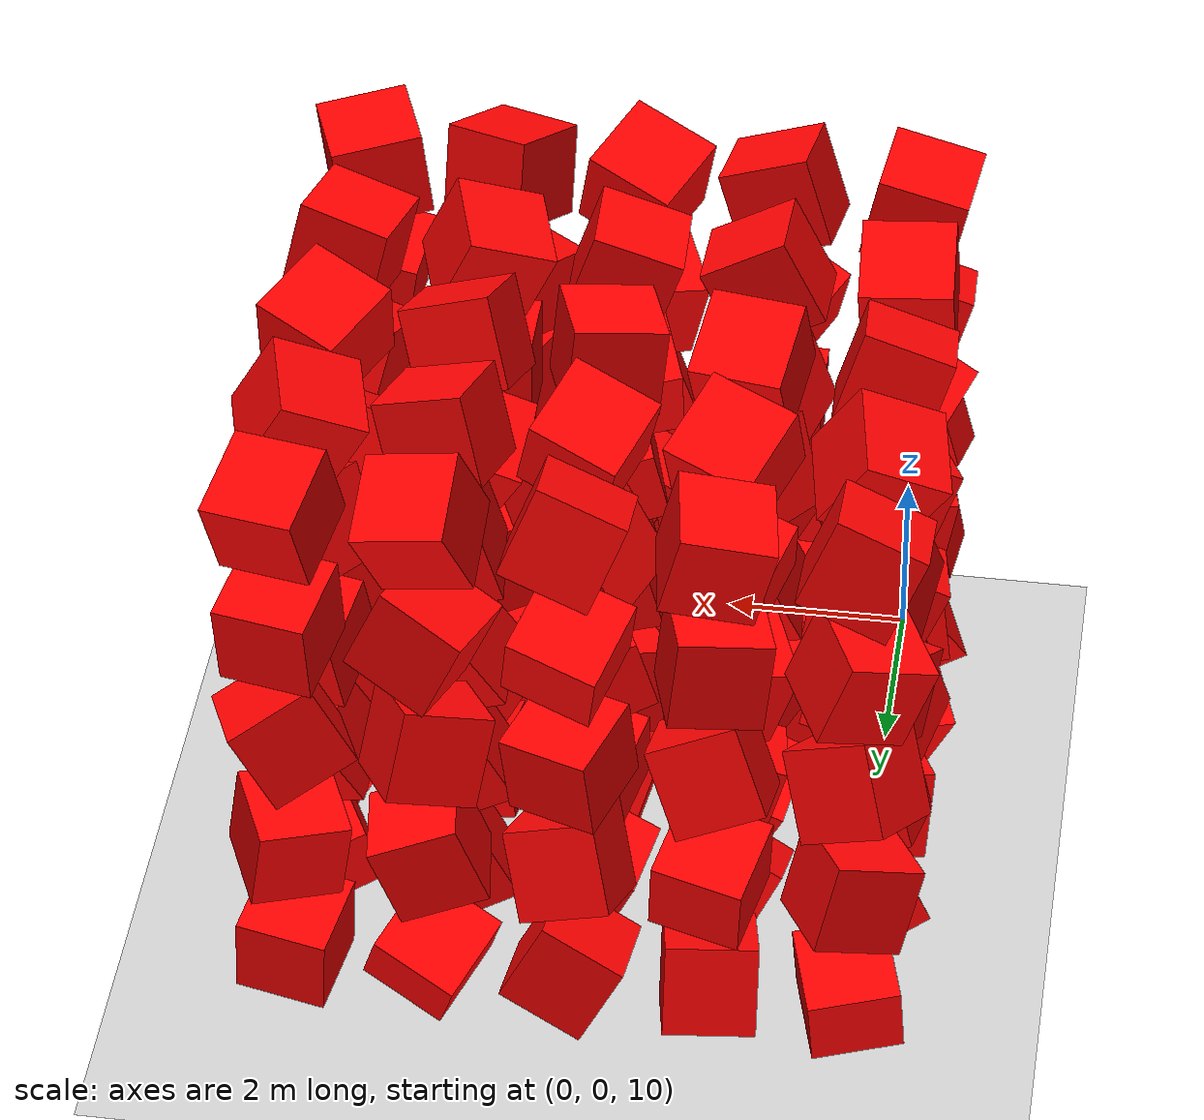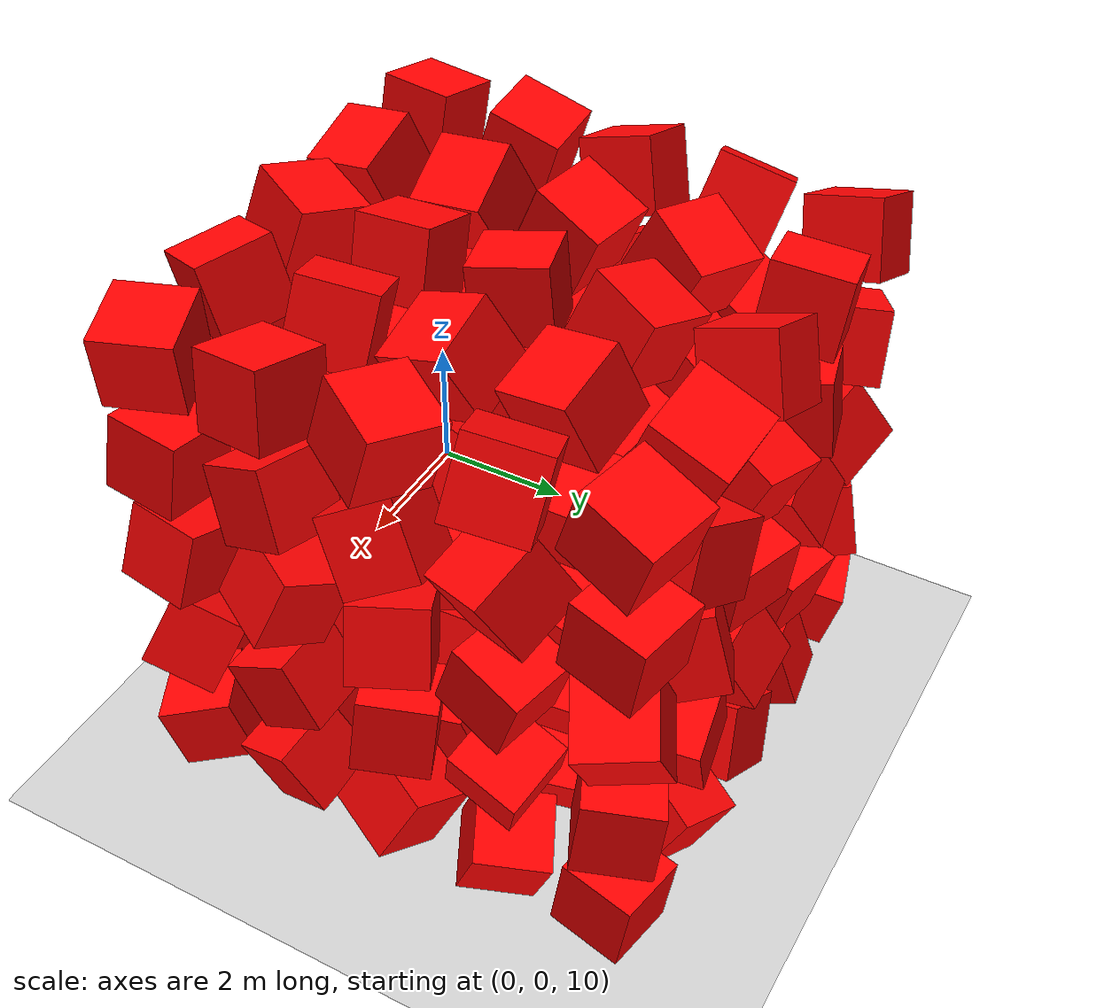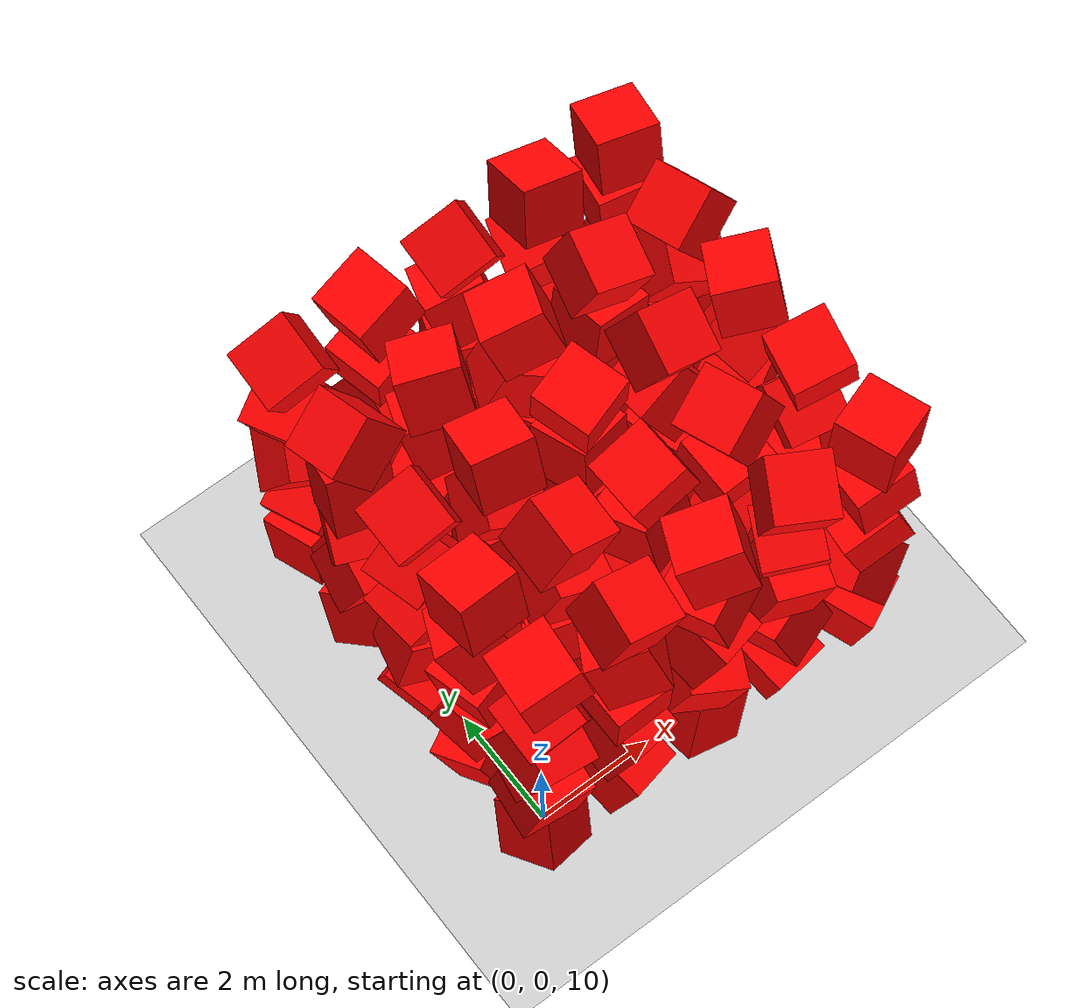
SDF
<sdf version='1.6'>
  <world name='default'>
    <model name='ground_plane'>
      <pose>0 0 9  0 0 0</pose>
      <static>1</static>
      <link name='link'>
        <collision name='collision'>
          <geometry>
            <plane>
              <normal>0 0 1</normal>
              <size>100 100</size>
            </plane>
          </geometry>
          <surface>
            <bounce>
              <restitution_coefficient>0</restitution_coefficient>
            </bounce>
          </surface>
        </collision>
        <visual name='visual'>
          <geometry>
            <plane>
              <normal>0 0 1</normal>
              <size>100 100</size>
            </plane>
          </geometry>
          <material>
            <ambient>0.8 0.8 0.8 1</ambient>
            <diffuse>0.8 0.8 0.8 1</diffuse>
            <specular>0.8 0.8 0.8 1</specular>
          </material>
        </visual>
      </link>
    </model>
    <model name='model_0_0_0'>
      <pose>0 0 10 -0.445969 0.437062 0.232212</pose>
      <link name='box_link'>
        <inertial>
          <inertia>
            <ixx>1</ixx>
            <ixy>0</ixy>
            <ixz>0</ixz>
            <iyy>1</iyy>
            <iyz>0</iyz>
            <izz>1</izz>
          </inertia>
          <mass>6</mass>
        </inertial>
        <collision name='box_collision'>
          <geometry>
            <box>
              <size>1 1 1</size>
            </box>
          </geometry>
          <surface>
            <bounce>
              <restitution_coefficient>0</restitution_coefficient>
            </bounce>
          </surface>
        </collision>
        <visual name='box_visual'>
          <geometry>
            <box>
              <size>1 1 1</size>
            </box>
          </geometry>
          <material>
            <ambient>1 0 0 1</ambient>
            <diffuse>1 0 0 1</diffuse>
            <specular>1 0 0 1</specular>
          </material>
        </visual>
      </link>
    </model>
    <model name='model_0_0_1'>
      <pose>0 0 11.5 0.162706 0.237268 -0.04658</pose>
      <link name='box_link'>
        <inertial>
          <inertia>
            <ixx>1</ixx>
            <ixy>0</ixy>
            <ixz>0</ixz>
            <iyy>1</iyy>
            <iyz>0</iyz>
            <izz>1</izz>
          </inertia>
          <mass>6</mass>
        </inertial>
        <collision name='box_collision'>
          <geometry>
            <box>
              <size>1 1 1</size>
            </box>
          </geometry>
          <surface>
            <bounce>
              <restitution_coefficient>0</restitution_coefficient>
            </bounce>
          </surface>
        </collision>
        <visual name='box_visual'>
          <geometry>
            <box>
              <size>1 1 1</size>
            </box>
          </geometry>
          <material>
            <ambient>1 0 0 1</ambient>
            <diffuse>1 0 0 1</diffuse>
            <specular>1 0 0 1</specular>
          </material>
        </visual>
      </link>
    </model>
    <model name='model_0_0_2'>
      <pose>0 0 13 0.353318 0.359839 0.00596</pose>
      <link name='box_link'>
        <inertial>
          <inertia>
            <ixx>1</ixx>
            <ixy>0</ixy>
            <ixz>0</ixz>
            <iyy>1</iyy>
            <iyz>0</iyz>
            <izz>1</izz>
          </inertia>
          <mass>6</mass>
        </inertial>
        <collision name='box_collision'>
          <geometry>
            <box>
              <size>1 1 1</size>
            </box>
          </geometry>
          <surface>
            <bounce>
              <restitution_coefficient>0</restitution_coefficient>
            </bounce>
          </surface>
        </collision>
        <visual name='box_visual'>
          <geometry>
            <box>
              <size>1 1 1</size>
            </box>
          </geometry>
          <material>
            <ambient>1 0 0 1</ambient>
            <diffuse>1 0 0 1</diffuse>
            <specular>1 0 0 1</specular>
          </material>
        </visual>
      </link>
    </model>
    <model name='model_0_0_3'>
      <pose>0 0 14.5 0.279494 -0.284371 -0.051229</pose>
      <link name='box_link'>
        <inertial>
          <inertia>
            <ixx>1</ixx>
            <ixy>0</ixy>
            <ixz>0</ixz>
            <iyy>1</iyy>
            <iyz>0</iyz>
            <izz>1</izz>
          </inertia>
          <mass>6</mass>
        </inertial>
        <collision name='box_collision'>
          <geometry>
            <box>
              <size>1 1 1</size>
            </box>
          </geometry>
          <surface>
            <bounce>
              <restitution_coefficient>0</restitution_coefficient>
            </bounce>
          </surface>
        </collision>
        <visual name='box_visual'>
          <geometry>
            <box>
              <size>1 1 1</size>
            </box>
          </geometry>
          <material>
            <ambient>1 0 0 1</ambient>
            <diffuse>1 0 0 1</diffuse>
            <specular>1 0 0 1</specular>
          </material>
        </visual>
      </link>
    </model>
    <model name='model_0_0_4'>
      <pose>0 0 16 -0.03669 -0.197186 -0.095349</pose>
      <link name='box_link'>
        <inertial>
          <inertia>
            <ixx>1</ixx>
            <ixy>0</ixy>
            <ixz>0</ixz>
            <iyy>1</iyy>
            <iyz>0</iyz>
            <izz>1</izz>
          </inertia>
          <mass>6</mass>
        </inertial>
        <collision name='box_collision'>
          <geometry>
            <box>
              <size>1 1 1</size>
            </box>
          </geometry>
          <surface>
            <bounce>
              <restitution_coefficient>0</restitution_coefficient>
            </bounce>
          </surface>
        </collision>
        <visual name='box_visual'>
          <geometry>
            <box>
              <size>1 1 1</size>
            </box>
          </geometry>
          <material>
            <ambient>1 0 0 1</ambient>
            <diffuse>1 0 0 1</diffuse>
            <specular>1 0 0 1</specular>
          </material>
        </visual>
      </link>
    </model>
    <model name='model_0_1_0'>
      <pose>0 1.5 10 -0.444529 -0.146822 0.471578</pose>
      <link name='box_link'>
        <inertial>
          <inertia>
            <ixx>1</ixx>
            <ixy>0</ixy>
            <ixz>0</ixz>
            <iyy>1</iyy>
            <iyz>0</iyz>
            <izz>1</izz>
          </inertia>
          <mass>6</mass>
        </inertial>
        <collision name='box_collision'>
          <geometry>
            <box>
              <size>1 1 1</size>
            </box>
          </geometry>
          <surface>
            <bounce>
              <restitution_coefficient>0</restitution_coefficient>
            </bounce>
          </surface>
        </collision>
        <visual name='box_visual'>
          <geometry>
            <box>
              <size>1 1 1</size>
            </box>
          </geometry>
          <material>
            <ambient>1 0 0 1</ambient>
            <diffuse>1 0 0 1</diffuse>
            <specular>1 0 0 1</specular>
          </material>
        </visual>
      </link>
    </model>
    <model name='model_0_1_1'>
      <pose>0 1.5 11.5 0.313697 0.087827 0.266329</pose>
      <link name='box_link'>
        <inertial>
          <inertia>
            <ixx>1</ixx>
            <ixy>0</ixy>
            <ixz>0</ixz>
            <iyy>1</iyy>
            <iyz>0</iyz>
            <izz>1</izz>
          </inertia>
          <mass>6</mass>
        </inertial>
        <collision name='box_collision'>
          <geometry>
            <box>
              <size>1 1 1</size>
            </box>
          </geometry>
          <surface>
            <bounce>
              <restitution_coefficient>0</restitution_coefficient>
            </bounce>
          </surface>
        </collision>
        <visual name='box_visual'>
          <geometry>
            <box>
              <size>1 1 1</size>
            </box>
          </geometry>
          <material>
            <ambient>1 0 0 1</ambient>
            <diffuse>1 0 0 1</diffuse>
            <specular>1 0 0 1</specular>
          </material>
        </visual>
      </link>
    </model>
    <model name='model_0_1_2'>
      <pose>0 1.5 13 -0.097363 -0.144194 0.248824</pose>
      <link name='box_link'>
        <inertial>
          <inertia>
            <ixx>1</ixx>
            <ixy>0</ixy>
            <ixz>0</ixz>
            <iyy>1</iyy>
            <iyz>0</iyz>
            <izz>1</izz>
          </inertia>
          <mass>6</mass>
        </inertial>
        <collision name='box_collision'>
          <geometry>
            <box>
              <size>1 1 1</size>
            </box>
          </geometry>
          <surface>
            <bounce>
              <restitution_coefficient>0</restitution_coefficient>
            </bounce>
          </surface>
        </collision>
        <visual name='box_visual'>
          <geometry>
            <box>
              <size>1 1 1</size>
            </box>
          </geometry>
          <material>
            <ambient>1 0 0 1</ambient>
            <diffuse>1 0 0 1</diffuse>
            <specular>1 0 0 1</specular>
          </material>
        </visual>
      </link>
    </model>
    <model name='model_0_1_3'>
      <pose>0 1.5 14.5 -0.411716 -0.452408 -0.238945</pose>
      <link name='box_link'>
        <inertial>
          <inertia>
            <ixx>1</ixx>
            <ixy>0</ixy>
            <ixz>0</ixz>
            <iyy>1</iyy>
            <iyz>0</iyz>
            <izz>1</izz>
          </inertia>
          <mass>6</mass>
        </inertial>
        <collision name='box_collision'>
          <geometry>
            <box>
              <size>1 1 1</size>
            </box>
          </geometry>
          <surface>
            <bounce>
              <restitution_coefficient>0</restitution_coefficient>
            </bounce>
          </surface>
        </collision>
        <visual name='box_visual'>
          <geometry>
            <box>
              <size>1 1 1</size>
            </box>
          </geometry>
          <material>
            <ambient>1 0 0 1</ambient>
            <diffuse>1 0 0 1</diffuse>
            <specular>1 0 0 1</specular>
          </material>
        </visual>
      </link>
    </model>
    <model name='model_0_1_4'>
      <pose>0 1.5 16 -0.301174 0.051928 0.040391</pose>
      <link name='box_link'>
        <inertial>
          <inertia>
            <ixx>1</ixx>
            <ixy>0</ixy>
            <ixz>0</ixz>
            <iyy>1</iyy>
            <iyz>0</iyz>
            <izz>1</izz>
          </inertia>
          <mass>6</mass>
        </inertial>
        <collision name='box_collision'>
          <geometry>
            <box>
              <size>1 1 1</size>
            </box>
          </geometry>
          <surface>
            <bounce>
              <restitution_coefficient>0</restitution_coefficient>
            </bounce>
          </surface>
        </collision>
        <visual name='box_visual'>
          <geometry>
            <box>
              <size>1 1 1</size>
            </box>
          </geometry>
          <material>
            <ambient>1 0 0 1</ambient>
            <diffuse>1 0 0 1</diffuse>
            <specular>1 0 0 1</specular>
          </material>
        </visual>
      </link>
    </model>
    <model name='model_0_2_0'>
      <pose>0 3 10 0.325412 -0.150021 0.2704</pose>
      <link name='box_link'>
        <inertial>
          <inertia>
            <ixx>1</ixx>
            <ixy>0</ixy>
            <ixz>0</ixz>
            <iyy>1</iyy>
            <iyz>0</iyz>
            <izz>1</izz>
          </inertia>
          <mass>6</mass>
        </inertial>
        <collision name='box_collision'>
          <geometry>
            <box>
              <size>1 1 1</size>
            </box>
          </geometry>
          <surface>
            <bounce>
              <restitution_coefficient>0</restitution_coefficient>
            </bounce>
          </surface>
        </collision>
        <visual name='box_visual'>
          <geometry>
            <box>
              <size>1 1 1</size>
            </box>
          </geometry>
          <material>
            <ambient>1 0 0 1</ambient>
            <diffuse>1 0 0 1</diffuse>
            <specular>1 0 0 1</specular>
          </material>
        </visual>
      </link>
    </model>
    <model name='model_0_2_1'>
      <pose>0 3 11.5 -0.094698 0.330572 -0.26515</pose>
      <link name='box_link'>
        <inertial>
          <inertia>
            <ixx>1</ixx>
            <ixy>0</ixy>
            <ixz>0</ixz>
            <iyy>1</iyy>
            <iyz>0</iyz>
            <izz>1</izz>
          </inertia>
          <mass>6</mass>
        </inertial>
        <collision name='box_collision'>
          <geometry>
            <box>
              <size>1 1 1</size>
            </box>
          </geometry>
          <surface>
            <bounce>
              <restitution_coefficient>0</restitution_coefficient>
            </bounce>
          </surface>
        </collision>
        <visual name='box_visual'>
          <geometry>
            <box>
              <size>1 1 1</size>
            </box>
          </geometry>
          <material>
            <ambient>1 0 0 1</ambient>
            <diffuse>1 0 0 1</diffuse>
            <specular>1 0 0 1</specular>
          </material>
        </visual>
      </link>
    </model>
    <model name='model_0_2_2'>
      <pose>0 3 13 0.198001 -0.426438 0.054277</pose>
      <link name='box_link'>
        <inertial>
          <inertia>
            <ixx>1</ixx>
            <ixy>0</ixy>
            <ixz>0</ixz>
            <iyy>1</iyy>
            <iyz>0</iyz>
            <izz>1</izz>
          </inertia>
          <mass>6</mass>
        </inertial>
        <collision name='box_collision'>
          <geometry>
            <box>
              <size>1 1 1</size>
            </box>
          </geometry>
          <surface>
            <bounce>
              <restitution_coefficient>0</restitution_coefficient>
            </bounce>
          </surface>
        </collision>
        <visual name='box_visual'>
          <geometry>
            <box>
              <size>1 1 1</size>
            </box>
          </geometry>
          <material>
            <ambient>1 0 0 1</ambient>
            <diffuse>1 0 0 1</diffuse>
            <specular>1 0 0 1</specular>
          </material>
        </visual>
      </link>
    </model>
    <model name='model_0_2_3'>
      <pose>0 3 14.5 0.263427 -0.444841 0.21894</pose>
      <link name='box_link'>
        <inertial>
          <inertia>
            <ixx>1</ixx>
            <ixy>0</ixy>
            <ixz>0</ixz>
            <iyy>1</iyy>
            <iyz>0</iyz>
            <izz>1</izz>
          </inertia>
          <mass>6</mass>
        </inertial>
        <collision name='box_collision'>
          <geometry>
            <box>
              <size>1 1 1</size>
            </box>
          </geometry>
          <surface>
            <bounce>
              <restitution_coefficient>0</restitution_coefficient>
            </bounce>
          </surface>
        </collision>
        <visual name='box_visual'>
          <geometry>
            <box>
              <size>1 1 1</size>
            </box>
          </geometry>
          <material>
            <ambient>1 0 0 1</ambient>
            <diffuse>1 0 0 1</diffuse>
            <specular>1 0 0 1</specular>
          </material>
        </visual>
      </link>
    </model>
    <model name='model_0_2_4'>
      <pose>0 3 16 0.292098 -0.297187 -0.040628</pose>
      <link name='box_link'>
        <inertial>
          <inertia>
            <ixx>1</ixx>
            <ixy>0</ixy>
            <ixz>0</ixz>
            <iyy>1</iyy>
            <iyz>0</iyz>
            <izz>1</izz>
          </inertia>
          <mass>6</mass>
        </inertial>
        <collision name='box_collision'>
          <geometry>
            <box>
              <size>1 1 1</size>
            </box>
          </geometry>
          <surface>
            <bounce>
              <restitution_coefficient>0</restitution_coefficient>
            </bounce>
          </surface>
        </collision>
        <visual name='box_visual'>
          <geometry>
            <box>
              <size>1 1 1</size>
            </box>
          </geometry>
          <material>
            <ambient>1 0 0 1</ambient>
            <diffuse>1 0 0 1</diffuse>
            <specular>1 0 0 1</specular>
          </material>
        </visual>
      </link>
    </model>
    <model name='model_0_3_0'>
      <pose>0 4.5 10 -0.417755 0.391808 0.464083</pose>
      <link name='box_link'>
        <inertial>
          <inertia>
            <ixx>1</ixx>
            <ixy>0</ixy>
            <ixz>0</ixz>
            <iyy>1</iyy>
            <iyz>0</iyz>
            <izz>1</izz>
          </inertia>
          <mass>6</mass>
        </inertial>
        <collision name='box_collision'>
          <geometry>
            <box>
              <size>1 1 1</size>
            </box>
          </geometry>
          <surface>
            <bounce>
              <restitution_coefficient>0</restitution_coefficient>
            </bounce>
          </surface>
        </collision>
        <visual name='box_visual'>
          <geometry>
            <box>
              <size>1 1 1</size>
            </box>
          </geometry>
          <material>
            <ambient>1 0 0 1</ambient>
            <diffuse>1 0 0 1</diffuse>
            <specular>1 0 0 1</specular>
          </material>
        </visual>
      </link>
    </model>
    <model name='model_0_3_1'>
      <pose>0 4.5 11.5 0.300886 0.329793 -0.049279</pose>
      <link name='box_link'>
        <inertial>
          <inertia>
            <ixx>1</ixx>
            <ixy>0</ixy>
            <ixz>0</ixz>
            <iyy>1</iyy>
            <iyz>0</iyz>
            <izz>1</izz>
          </inertia>
          <mass>6</mass>
        </inertial>
        <collision name='box_collision'>
          <geometry>
            <box>
              <size>1 1 1</size>
            </box>
          </geometry>
          <surface>
            <bounce>
              <restitution_coefficient>0</restitution_coefficient>
            </bounce>
          </surface>
        </collision>
        <visual name='box_visual'>
          <geometry>
            <box>
              <size>1 1 1</size>
            </box>
          </geometry>
          <material>
            <ambient>1 0 0 1</ambient>
            <diffuse>1 0 0 1</diffuse>
            <specular>1 0 0 1</specular>
          </material>
        </visual>
      </link>
    </model>
    <model name='model_0_3_2'>
      <pose>0 4.5 13 0.46908 0.010174 -0.382881</pose>
      <link name='box_link'>
        <inertial>
          <inertia>
            <ixx>1</ixx>
            <ixy>0</ixy>
            <ixz>0</ixz>
            <iyy>1</iyy>
            <iyz>0</iyz>
            <izz>1</izz>
          </inertia>
          <mass>6</mass>
        </inertial>
        <collision name='box_collision'>
          <geometry>
            <box>
              <size>1 1 1</size>
            </box>
          </geometry>
          <surface>
            <bounce>
              <restitution_coefficient>0</restitution_coefficient>
            </bounce>
          </surface>
        </collision>
        <visual name='box_visual'>
          <geometry>
            <box>
              <size>1 1 1</size>
            </box>
          </geometry>
          <material>
            <ambient>1 0 0 1</ambient>
            <diffuse>1 0 0 1</diffuse>
            <specular>1 0 0 1</specular>
          </material>
        </visual>
      </link>
    </model>
    <model name='model_0_3_3'>
      <pose>0 4.5 14.5 -0.49055 0.081027 -0.24292</pose>
      <link name='box_link'>
        <inertial>
          <inertia>
            <ixx>1</ixx>
            <ixy>0</ixy>
            <ixz>0</ixz>
            <iyy>1</iyy>
            <iyz>0</iyz>
            <izz>1</izz>
          </inertia>
          <mass>6</mass>
        </inertial>
        <collision name='box_collision'>
          <geometry>
            <box>
              <size>1 1 1</size>
            </box>
          </geometry>
          <surface>
            <bounce>
              <restitution_coefficient>0</restitution_coefficient>
            </bounce>
          </surface>
        </collision>
        <visual name='box_visual'>
          <geometry>
            <box>
              <size>1 1 1</size>
            </box>
          </geometry>
          <material>
            <ambient>1 0 0 1</ambient>
            <diffuse>1 0 0 1</diffuse>
            <specular>1 0 0 1</specular>
          </material>
        </visual>
      </link>
    </model>
    <model name='model_0_3_4'>
      <pose>0 4.5 16 -0.314394 -0.475655 0.323114</pose>
      <link name='box_link'>
        <inertial>
          <inertia>
            <ixx>1</ixx>
            <ixy>0</ixy>
            <ixz>0</ixz>
            <iyy>1</iyy>
            <iyz>0</iyz>
            <izz>1</izz>
          </inertia>
          <mass>6</mass>
        </inertial>
        <collision name='box_collision'>
          <geometry>
            <box>
              <size>1 1 1</size>
            </box>
          </geometry>
          <surface>
            <bounce>
              <restitution_coefficient>0</restitution_coefficient>
            </bounce>
          </surface>
        </collision>
        <visual name='box_visual'>
          <geometry>
            <box>
              <size>1 1 1</size>
            </box>
          </geometry>
          <material>
            <ambient>1 0 0 1</ambient>
            <diffuse>1 0 0 1</diffuse>
            <specular>1 0 0 1</specular>
          </material>
        </visual>
      </link>
    </model>
    <model name='model_0_4_0'>
      <pose>0 6 10 -0.227574 0.107794 0.261805</pose>
      <link name='box_link'>
        <inertial>
          <inertia>
            <ixx>1</ixx>
            <ixy>0</ixy>
            <ixz>0</ixz>
            <iyy>1</iyy>
            <iyz>0</iyz>
            <izz>1</izz>
          </inertia>
          <mass>6</mass>
        </inertial>
        <collision name='box_collision'>
          <geometry>
            <box>
              <size>1 1 1</size>
            </box>
          </geometry>
          <surface>
            <bounce>
              <restitution_coefficient>0</restitution_coefficient>
            </bounce>
          </surface>
        </collision>
        <visual name='box_visual'>
          <geometry>
            <box>
              <size>1 1 1</size>
            </box>
          </geometry>
          <material>
            <ambient>1 0 0 1</ambient>
            <diffuse>1 0 0 1</diffuse>
            <specular>1 0 0 1</specular>
          </material>
        </visual>
      </link>
    </model>
    <model name='model_0_4_1'>
      <pose>0 6 11.5 0.170217 -0.314235 0.418764</pose>
      <link name='box_link'>
        <inertial>
          <inertia>
            <ixx>1</ixx>
            <ixy>0</ixy>
            <ixz>0</ixz>
            <iyy>1</iyy>
            <iyz>0</iyz>
            <izz>1</izz>
          </inertia>
          <mass>6</mass>
        </inertial>
        <collision name='box_collision'>
          <geometry>
            <box>
              <size>1 1 1</size>
            </box>
          </geometry>
          <surface>
            <bounce>
              <restitution_coefficient>0</restitution_coefficient>
            </bounce>
          </surface>
        </collision>
        <visual name='box_visual'>
          <geometry>
            <box>
              <size>1 1 1</size>
            </box>
          </geometry>
          <material>
            <ambient>1 0 0 1</ambient>
            <diffuse>1 0 0 1</diffuse>
            <specular>1 0 0 1</specular>
          </material>
        </visual>
      </link>
    </model>
    <model name='model_0_4_2'>
      <pose>0 6 13 0.400062 0.448993 -0.292275</pose>
      <link name='box_link'>
        <inertial>
          <inertia>
            <ixx>1</ixx>
            <ixy>0</ixy>
            <ixz>0</ixz>
            <iyy>1</iyy>
            <iyz>0</iyz>
            <izz>1</izz>
          </inertia>
          <mass>6</mass>
        </inertial>
        <collision name='box_collision'>
          <geometry>
            <box>
              <size>1 1 1</size>
            </box>
          </geometry>
          <surface>
            <bounce>
              <restitution_coefficient>0</restitution_coefficient>
            </bounce>
          </surface>
        </collision>
        <visual name='box_visual'>
          <geometry>
            <box>
              <size>1 1 1</size>
            </box>
          </geometry>
          <material>
            <ambient>1 0 0 1</ambient>
            <diffuse>1 0 0 1</diffuse>
            <specular>1 0 0 1</specular>
          </material>
        </visual>
      </link>
    </model>
    <model name='model_0_4_3'>
      <pose>0 6 14.5 -0.092668 -0.332408 0.475542</pose>
      <link name='box_link'>
        <inertial>
          <inertia>
            <ixx>1</ixx>
            <ixy>0</ixy>
            <ixz>0</ixz>
            <iyy>1</iyy>
            <iyz>0</iyz>
            <izz>1</izz>
          </inertia>
          <mass>6</mass>
        </inertial>
        <collision name='box_collision'>
          <geometry>
            <box>
              <size>1 1 1</size>
            </box>
          </geometry>
          <surface>
            <bounce>
              <restitution_coefficient>0</restitution_coefficient>
            </bounce>
          </surface>
        </collision>
        <visual name='box_visual'>
          <geometry>
            <box>
              <size>1 1 1</size>
            </box>
          </geometry>
          <material>
            <ambient>1 0 0 1</ambient>
            <diffuse>1 0 0 1</diffuse>
            <specular>1 0 0 1</specular>
          </material>
        </visual>
      </link>
    </model>
    <model name='model_0_4_4'>
      <pose>0 6 16 0.257004 -0.379118 -0.092636</pose>
      <link name='box_link'>
        <inertial>
          <inertia>
            <ixx>1</ixx>
            <ixy>0</ixy>
            <ixz>0</ixz>
            <iyy>1</iyy>
            <iyz>0</iyz>
            <izz>1</izz>
          </inertia>
          <mass>6</mass>
        </inertial>
        <collision name='box_collision'>
          <geometry>
            <box>
              <size>1 1 1</size>
            </box>
          </geometry>
          <surface>
            <bounce>
              <restitution_coefficient>0</restitution_coefficient>
            </bounce>
          </surface>
        </collision>
        <visual name='box_visual'>
          <geometry>
            <box>
              <size>1 1 1</size>
            </box>
          </geometry>
          <material>
            <ambient>1 0 0 1</ambient>
            <diffuse>1 0 0 1</diffuse>
            <specular>1 0 0 1</specular>
          </material>
        </visual>
      </link>
    </model>
    <model name='model_1_0_0'>
      <pose>1.5 0 10 0.354994 0.245428 0.266498</pose>
      <link name='box_link'>
        <inertial>
          <inertia>
            <ixx>1</ixx>
            <ixy>0</ixy>
            <ixz>0</ixz>
            <iyy>1</iyy>
            <iyz>0</iyz>
            <izz>1</izz>
          </inertia>
          <mass>6</mass>
        </inertial>
        <collision name='box_collision'>
          <geometry>
            <box>
              <size>1 1 1</size>
            </box>
          </geometry>
          <surface>
            <bounce>
              <restitution_coefficient>0</restitution_coefficient>
            </bounce>
          </surface>
        </collision>
        <visual name='box_visual'>
          <geometry>
            <box>
              <size>1 1 1</size>
            </box>
          </geometry>
          <material>
            <ambient>1 0 0 1</ambient>
            <diffuse>1 0 0 1</diffuse>
            <specular>1 0 0 1</specular>
          </material>
        </visual>
      </link>
    </model>
    <model name='model_1_0_1'>
      <pose>1.5 0 11.5 0.331195 0.322869 0.196046</pose>
      <link name='box_link'>
        <inertial>
          <inertia>
            <ixx>1</ixx>
            <ixy>0</ixy>
            <ixz>0</ixz>
            <iyy>1</iyy>
            <iyz>0</iyz>
            <izz>1</izz>
          </inertia>
          <mass>6</mass>
        </inertial>
        <collision name='box_collision'>
          <geometry>
            <box>
              <size>1 1 1</size>
            </box>
          </geometry>
          <surface>
            <bounce>
              <restitution_coefficient>0</restitution_coefficient>
            </bounce>
          </surface>
        </collision>
        <visual name='box_visual'>
          <geometry>
            <box>
              <size>1 1 1</size>
            </box>
          </geometry>
          <material>
            <ambient>1 0 0 1</ambient>
            <diffuse>1 0 0 1</diffuse>
            <specular>1 0 0 1</specular>
          </material>
        </visual>
      </link>
    </model>
    <model name='model_1_0_2'>
      <pose>1.5 0 13 0.068366 -0.022949 0.020605</pose>
      <link name='box_link'>
        <inertial>
          <inertia>
            <ixx>1</ixx>
            <ixy>0</ixy>
            <ixz>0</ixz>
            <iyy>1</iyy>
            <iyz>0</iyz>
            <izz>1</izz>
          </inertia>
          <mass>6</mass>
        </inertial>
        <collision name='box_collision'>
          <geometry>
            <box>
              <size>1 1 1</size>
            </box>
          </geometry>
          <surface>
            <bounce>
              <restitution_coefficient>0</restitution_coefficient>
            </bounce>
          </surface>
        </collision>
        <visual name='box_visual'>
          <geometry>
            <box>
              <size>1 1 1</size>
            </box>
          </geometry>
          <material>
            <ambient>1 0 0 1</ambient>
            <diffuse>1 0 0 1</diffuse>
            <specular>1 0 0 1</specular>
          </material>
        </visual>
      </link>
    </model>
    <model name='model_1_0_3'>
      <pose>1.5 0 14.5 -0.299301 -0.334679 -0.422738</pose>
      <link name='box_link'>
        <inertial>
          <inertia>
            <ixx>1</ixx>
            <ixy>0</ixy>
            <ixz>0</ixz>
            <iyy>1</iyy>
            <iyz>0</iyz>
            <izz>1</izz>
          </inertia>
          <mass>6</mass>
        </inertial>
        <collision name='box_collision'>
          <geometry>
            <box>
              <size>1 1 1</size>
            </box>
          </geometry>
          <surface>
            <bounce>
              <restitution_coefficient>0</restitution_coefficient>
            </bounce>
          </surface>
        </collision>
        <visual name='box_visual'>
          <geometry>
            <box>
              <size>1 1 1</size>
            </box>
          </geometry>
          <material>
            <ambient>1 0 0 1</ambient>
            <diffuse>1 0 0 1</diffuse>
            <specular>1 0 0 1</specular>
          </material>
        </visual>
      </link>
    </model>
    <model name='model_1_0_4'>
      <pose>1.5 0 16 0.187896 0.342837 -0.038506</pose>
      <link name='box_link'>
        <inertial>
          <inertia>
            <ixx>1</ixx>
            <ixy>0</ixy>
            <ixz>0</ixz>
            <iyy>1</iyy>
            <iyz>0</iyz>
            <izz>1</izz>
          </inertia>
          <mass>6</mass>
        </inertial>
        <collision name='box_collision'>
          <geometry>
            <box>
              <size>1 1 1</size>
            </box>
          </geometry>
          <surface>
            <bounce>
              <restitution_coefficient>0</restitution_coefficient>
            </bounce>
          </surface>
        </collision>
        <visual name='box_visual'>
          <geometry>
            <box>
              <size>1 1 1</size>
            </box>
          </geometry>
          <material>
            <ambient>1 0 0 1</ambient>
            <diffuse>1 0 0 1</diffuse>
            <specular>1 0 0 1</specular>
          </material>
        </visual>
      </link>
    </model>
    <model name='model_1_1_0'>
      <pose>1.5 1.5 10 -0.175396 0.200267 0.47763</pose>
      <link name='box_link'>
        <inertial>
          <inertia>
            <ixx>1</ixx>
            <ixy>0</ixy>
            <ixz>0</ixz>
            <iyy>1</iyy>
            <iyz>0</iyz>
            <izz>1</izz>
          </inertia>
          <mass>6</mass>
        </inertial>
        <collision name='box_collision'>
          <geometry>
            <box>
              <size>1 1 1</size>
            </box>
          </geometry>
          <surface>
            <bounce>
              <restitution_coefficient>0</restitution_coefficient>
            </bounce>
          </surface>
        </collision>
        <visual name='box_visual'>
          <geometry>
            <box>
              <size>1 1 1</size>
            </box>
          </geometry>
          <material>
            <ambient>1 0 0 1</ambient>
            <diffuse>1 0 0 1</diffuse>
            <specular>1 0 0 1</specular>
          </material>
        </visual>
      </link>
    </model>
    <model name='model_1_1_1'>
      <pose>1.5 1.5 11.5 -0.395518 -0.123414 0.050976</pose>
      <link name='box_link'>
        <inertial>
          <inertia>
            <ixx>1</ixx>
            <ixy>0</ixy>
            <ixz>0</ixz>
            <iyy>1</iyy>
            <iyz>0</iyz>
            <izz>1</izz>
          </inertia>
          <mass>6</mass>
        </inertial>
        <collision name='box_collision'>
          <geometry>
            <box>
              <size>1 1 1</size>
            </box>
          </geometry>
          <surface>
            <bounce>
              <restitution_coefficient>0</restitution_coefficient>
            </bounce>
          </surface>
        </collision>
        <visual name='box_visual'>
          <geometry>
            <box>
              <size>1 1 1</size>
            </box>
          </geometry>
          <material>
            <ambient>1 0 0 1</ambient>
            <diffuse>1 0 0 1</diffuse>
            <specular>1 0 0 1</specular>
          </material>
        </visual>
      </link>
    </model>
    <model name='model_1_1_2'>
      <pose>1.5 1.5 13 -0.183462 -0.18323 -0.351025</pose>
      <link name='box_link'>
        <inertial>
          <inertia>
            <ixx>1</ixx>
            <ixy>0</ixy>
            <ixz>0</ixz>
            <iyy>1</iyy>
            <iyz>0</iyz>
            <izz>1</izz>
          </inertia>
          <mass>6</mass>
        </inertial>
        <collision name='box_collision'>
          <geometry>
            <box>
              <size>1 1 1</size>
            </box>
          </geometry>
          <surface>
            <bounce>
              <restitution_coefficient>0</restitution_coefficient>
            </bounce>
          </surface>
        </collision>
        <visual name='box_visual'>
          <geometry>
            <box>
              <size>1 1 1</size>
            </box>
          </geometry>
          <material>
            <ambient>1 0 0 1</ambient>
            <diffuse>1 0 0 1</diffuse>
            <specular>1 0 0 1</specular>
          </material>
        </visual>
      </link>
    </model>
    <model name='model_1_1_3'>
      <pose>1.5 1.5 14.5 0.096896 0.428017 -0.173226</pose>
      <link name='box_link'>
        <inertial>
          <inertia>
            <ixx>1</ixx>
            <ixy>0</ixy>
            <ixz>0</ixz>
            <iyy>1</iyy>
            <iyz>0</iyz>
            <izz>1</izz>
          </inertia>
          <mass>6</mass>
        </inertial>
        <collision name='box_collision'>
          <geometry>
            <box>
              <size>1 1 1</size>
            </box>
          </geometry>
          <surface>
            <bounce>
              <restitution_coefficient>0</restitution_coefficient>
            </bounce>
          </surface>
        </collision>
        <visual name='box_visual'>
          <geometry>
            <box>
              <size>1 1 1</size>
            </box>
          </geometry>
          <material>
            <ambient>1 0 0 1</ambient>
            <diffuse>1 0 0 1</diffuse>
            <specular>1 0 0 1</specular>
          </material>
        </visual>
      </link>
    </model>
    <model name='model_1_1_4'>
      <pose>1.5 1.5 16 0.131744 0.494762 0.05059</pose>
      <link name='box_link'>
        <inertial>
          <inertia>
            <ixx>1</ixx>
            <ixy>0</ixy>
            <ixz>0</ixz>
            <iyy>1</iyy>
            <iyz>0</iyz>
            <izz>1</izz>
          </inertia>
          <mass>6</mass>
        </inertial>
        <collision name='box_collision'>
          <geometry>
            <box>
              <size>1 1 1</size>
            </box>
          </geometry>
          <surface>
            <bounce>
              <restitution_coefficient>0</restitution_coefficient>
            </bounce>
          </surface>
        </collision>
        <visual name='box_visual'>
          <geometry>
            <box>
              <size>1 1 1</size>
            </box>
          </geometry>
          <material>
            <ambient>1 0 0 1</ambient>
            <diffuse>1 0 0 1</diffuse>
            <specular>1 0 0 1</specular>
          </material>
        </visual>
      </link>
    </model>
    <model name='model_1_2_0'>
      <pose>1.5 3 10 -0.304631 -0.370278 -0.084566</pose>
      <link name='box_link'>
        <inertial>
          <inertia>
            <ixx>1</ixx>
            <ixy>0</ixy>
            <ixz>0</ixz>
            <iyy>1</iyy>
            <iyz>0</iyz>
            <izz>1</izz>
          </inertia>
          <mass>6</mass>
        </inertial>
        <collision name='box_collision'>
          <geometry>
            <box>
              <size>1 1 1</size>
            </box>
          </geometry>
          <surface>
            <bounce>
              <restitution_coefficient>0</restitution_coefficient>
            </bounce>
          </surface>
        </collision>
        <visual name='box_visual'>
          <geometry>
            <box>
              <size>1 1 1</size>
            </box>
          </geometry>
          <material>
            <ambient>1 0 0 1</ambient>
            <diffuse>1 0 0 1</diffuse>
            <specular>1 0 0 1</specular>
          </material>
        </visual>
      </link>
    </model>
    <model name='model_1_2_1'>
      <pose>1.5 3 11.5 -0.072463 -0.069379 -0.4</pose>
      <link name='box_link'>
        <inertial>
          <inertia>
            <ixx>1</ixx>
            <ixy>0</ixy>
            <ixz>0</ixz>
            <iyy>1</iyy>
            <iyz>0</iyz>
            <izz>1</izz>
          </inertia>
          <mass>6</mass>
        </inertial>
        <collision name='box_collision'>
          <geometry>
            <box>
              <size>1 1 1</size>
            </box>
          </geometry>
          <surface>
            <bounce>
              <restitution_coefficient>0</restitution_coefficient>
            </bounce>
          </surface>
        </collision>
        <visual name='box_visual'>
          <geometry>
            <box>
              <size>1 1 1</size>
            </box>
          </geometry>
          <material>
            <ambient>1 0 0 1</ambient>
            <diffuse>1 0 0 1</diffuse>
            <specular>1 0 0 1</specular>
          </material>
        </visual>
      </link>
    </model>
    <model name='model_1_2_2'>
      <pose>1.5 3 13 -0.402596 0.243529 -0.040504</pose>
      <link name='box_link'>
        <inertial>
          <inertia>
            <ixx>1</ixx>
            <ixy>0</ixy>
            <ixz>0</ixz>
            <iyy>1</iyy>
            <iyz>0</iyz>
            <izz>1</izz>
          </inertia>
          <mass>6</mass>
        </inertial>
        <collision name='box_collision'>
          <geometry>
            <box>
              <size>1 1 1</size>
            </box>
          </geometry>
          <surface>
            <bounce>
              <restitution_coefficient>0</restitution_coefficient>
            </bounce>
          </surface>
        </collision>
        <visual name='box_visual'>
          <geometry>
            <box>
              <size>1 1 1</size>
            </box>
          </geometry>
          <material>
            <ambient>1 0 0 1</ambient>
            <diffuse>1 0 0 1</diffuse>
            <specular>1 0 0 1</specular>
          </material>
        </visual>
      </link>
    </model>
    <model name='model_1_2_3'>
      <pose>1.5 3 14.5 0.31041 0.428389 -0.304969</pose>
      <link name='box_link'>
        <inertial>
          <inertia>
            <ixx>1</ixx>
            <ixy>0</ixy>
            <ixz>0</ixz>
            <iyy>1</iyy>
            <iyz>0</iyz>
            <izz>1</izz>
          </inertia>
          <mass>6</mass>
        </inertial>
        <collision name='box_collision'>
          <geometry>
            <box>
              <size>1 1 1</size>
            </box>
          </geometry>
          <surface>
            <bounce>
              <restitution_coefficient>0</restitution_coefficient>
            </bounce>
          </surface>
        </collision>
        <visual name='box_visual'>
          <geometry>
            <box>
              <size>1 1 1</size>
            </box>
          </geometry>
          <material>
            <ambient>1 0 0 1</ambient>
            <diffuse>1 0 0 1</diffuse>
            <specular>1 0 0 1</specular>
          </material>
        </visual>
      </link>
    </model>
    <model name='model_1_2_4'>
      <pose>1.5 3 16 -0.401715 0.014026 -0.178878</pose>
      <link name='box_link'>
        <inertial>
          <inertia>
            <ixx>1</ixx>
            <ixy>0</ixy>
            <ixz>0</ixz>
            <iyy>1</iyy>
            <iyz>0</iyz>
            <izz>1</izz>
          </inertia>
          <mass>6</mass>
        </inertial>
        <collision name='box_collision'>
          <geometry>
            <box>
              <size>1 1 1</size>
            </box>
          </geometry>
          <surface>
            <bounce>
              <restitution_coefficient>0</restitution_coefficient>
            </bounce>
          </surface>
        </collision>
        <visual name='box_visual'>
          <geometry>
            <box>
              <size>1 1 1</size>
            </box>
          </geometry>
          <material>
            <ambient>1 0 0 1</ambient>
            <diffuse>1 0 0 1</diffuse>
            <specular>1 0 0 1</specular>
          </material>
        </visual>
      </link>
    </model>
    <model name='model_1_3_0'>
      <pose>1.5 4.5 10 0.478232 -0.401519 -0.246683</pose>
      <link name='box_link'>
        <inertial>
          <inertia>
            <ixx>1</ixx>
            <ixy>0</ixy>
            <ixz>0</ixz>
            <iyy>1</iyy>
            <iyz>0</iyz>
            <izz>1</izz>
          </inertia>
          <mass>6</mass>
        </inertial>
        <collision name='box_collision'>
          <geometry>
            <box>
              <size>1 1 1</size>
            </box>
          </geometry>
          <surface>
            <bounce>
              <restitution_coefficient>0</restitution_coefficient>
            </bounce>
          </surface>
        </collision>
        <visual name='box_visual'>
          <geometry>
            <box>
              <size>1 1 1</size>
            </box>
          </geometry>
          <material>
            <ambient>1 0 0 1</ambient>
            <diffuse>1 0 0 1</diffuse>
            <specular>1 0 0 1</specular>
          </material>
        </visual>
      </link>
    </model>
    <model name='model_1_3_1'>
      <pose>1.5 4.5 11.5 0.205103 -0.295949 0.05506</pose>
      <link name='box_link'>
        <inertial>
          <inertia>
            <ixx>1</ixx>
            <ixy>0</ixy>
            <ixz>0</ixz>
            <iyy>1</iyy>
            <iyz>0</iyz>
            <izz>1</izz>
          </inertia>
          <mass>6</mass>
        </inertial>
        <collision name='box_collision'>
          <geometry>
            <box>
              <size>1 1 1</size>
            </box>
          </geometry>
          <surface>
            <bounce>
              <restitution_coefficient>0</restitution_coefficient>
            </bounce>
          </surface>
        </collision>
        <visual name='box_visual'>
          <geometry>
            <box>
              <size>1 1 1</size>
            </box>
          </geometry>
          <material>
            <ambient>1 0 0 1</ambient>
            <diffuse>1 0 0 1</diffuse>
            <specular>1 0 0 1</specular>
          </material>
        </visual>
      </link>
    </model>
    <model name='model_1_3_2'>
      <pose>1.5 4.5 13 -0.134601 -0.289928 0.411441</pose>
      <link name='box_link'>
        <inertial>
          <inertia>
            <ixx>1</ixx>
            <ixy>0</ixy>
            <ixz>0</ixz>
            <iyy>1</iyy>
            <iyz>0</iyz>
            <izz>1</izz>
          </inertia>
          <mass>6</mass>
        </inertial>
        <collision name='box_collision'>
          <geometry>
            <box>
              <size>1 1 1</size>
            </box>
          </geometry>
          <surface>
            <bounce>
              <restitution_coefficient>0</restitution_coefficient>
            </bounce>
          </surface>
        </collision>
        <visual name='box_visual'>
          <geometry>
            <box>
              <size>1 1 1</size>
            </box>
          </geometry>
          <material>
            <ambient>1 0 0 1</ambient>
            <diffuse>1 0 0 1</diffuse>
            <specular>1 0 0 1</specular>
          </material>
        </visual>
      </link>
    </model>
    <model name='model_1_3_3'>
      <pose>1.5 4.5 14.5 -0.423302 -0.205102 -0.28686</pose>
      <link name='box_link'>
        <inertial>
          <inertia>
            <ixx>1</ixx>
            <ixy>0</ixy>
            <ixz>0</ixz>
            <iyy>1</iyy>
            <iyz>0</iyz>
            <izz>1</izz>
          </inertia>
          <mass>6</mass>
        </inertial>
        <collision name='box_collision'>
          <geometry>
            <box>
              <size>1 1 1</size>
            </box>
          </geometry>
          <surface>
            <bounce>
              <restitution_coefficient>0</restitution_coefficient>
            </bounce>
          </surface>
        </collision>
        <visual name='box_visual'>
          <geometry>
            <box>
              <size>1 1 1</size>
            </box>
          </geometry>
          <material>
            <ambient>1 0 0 1</ambient>
            <diffuse>1 0 0 1</diffuse>
            <specular>1 0 0 1</specular>
          </material>
        </visual>
      </link>
    </model>
    <model name='model_1_3_4'>
      <pose>1.5 4.5 16 -0.425594 -0.138593 -0.41062</pose>
      <link name='box_link'>
        <inertial>
          <inertia>
            <ixx>1</ixx>
            <ixy>0</ixy>
            <ixz>0</ixz>
            <iyy>1</iyy>
            <iyz>0</iyz>
            <izz>1</izz>
          </inertia>
          <mass>6</mass>
        </inertial>
        <collision name='box_collision'>
          <geometry>
            <box>
              <size>1 1 1</size>
            </box>
          </geometry>
          <surface>
            <bounce>
              <restitution_coefficient>0</restitution_coefficient>
            </bounce>
          </surface>
        </collision>
        <visual name='box_visual'>
          <geometry>
            <box>
              <size>1 1 1</size>
            </box>
          </geometry>
          <material>
            <ambient>1 0 0 1</ambient>
            <diffuse>1 0 0 1</diffuse>
            <specular>1 0 0 1</specular>
          </material>
        </visual>
      </link>
    </model>
    <model name='model_1_4_0'>
      <pose>1.5 6 10 0.369977 -0.03656 0.142431</pose>
      <link name='box_link'>
        <inertial>
          <inertia>
            <ixx>1</ixx>
            <ixy>0</ixy>
            <ixz>0</ixz>
            <iyy>1</iyy>
            <iyz>0</iyz>
            <izz>1</izz>
          </inertia>
          <mass>6</mass>
        </inertial>
        <collision name='box_collision'>
          <geometry>
            <box>
              <size>1 1 1</size>
            </box>
          </geometry>
          <surface>
            <bounce>
              <restitution_coefficient>0</restitution_coefficient>
            </bounce>
          </surface>
        </collision>
        <visual name='box_visual'>
          <geometry>
            <box>
              <size>1 1 1</size>
            </box>
          </geometry>
          <material>
            <ambient>1 0 0 1</ambient>
            <diffuse>1 0 0 1</diffuse>
            <specular>1 0 0 1</specular>
          </material>
        </visual>
      </link>
    </model>
    <model name='model_1_4_1'>
      <pose>1.5 6 11.5 -0.218769 -0.102826 -0.212903</pose>
      <link name='box_link'>
        <inertial>
          <inertia>
            <ixx>1</ixx>
            <ixy>0</ixy>
            <ixz>0</ixz>
            <iyy>1</iyy>
            <iyz>0</iyz>
            <izz>1</izz>
          </inertia>
          <mass>6</mass>
        </inertial>
        <collision name='box_collision'>
          <geometry>
            <box>
              <size>1 1 1</size>
            </box>
          </geometry>
          <surface>
            <bounce>
              <restitution_coefficient>0</restitution_coefficient>
            </bounce>
          </surface>
        </collision>
        <visual name='box_visual'>
          <geometry>
            <box>
              <size>1 1 1</size>
            </box>
          </geometry>
          <material>
            <ambient>1 0 0 1</ambient>
            <diffuse>1 0 0 1</diffuse>
            <specular>1 0 0 1</specular>
          </material>
        </visual>
      </link>
    </model>
    <model name='model_1_4_2'>
      <pose>1.5 6 13 0.403949 0.377601 0.111663</pose>
      <link name='box_link'>
        <inertial>
          <inertia>
            <ixx>1</ixx>
            <ixy>0</ixy>
            <ixz>0</ixz>
            <iyy>1</iyy>
            <iyz>0</iyz>
            <izz>1</izz>
          </inertia>
          <mass>6</mass>
        </inertial>
        <collision name='box_collision'>
          <geometry>
            <box>
              <size>1 1 1</size>
            </box>
          </geometry>
          <surface>
            <bounce>
              <restitution_coefficient>0</restitution_coefficient>
            </bounce>
          </surface>
        </collision>
        <visual name='box_visual'>
          <geometry>
            <box>
              <size>1 1 1</size>
            </box>
          </geometry>
          <material>
            <ambient>1 0 0 1</ambient>
            <diffuse>1 0 0 1</diffuse>
            <specular>1 0 0 1</specular>
          </material>
        </visual>
      </link>
    </model>
    <model name='model_1_4_3'>
      <pose>1.5 6 14.5 0.121707 -0.125929 0.244155</pose>
      <link name='box_link'>
        <inertial>
          <inertia>
            <ixx>1</ixx>
            <ixy>0</ixy>
            <ixz>0</ixz>
            <iyy>1</iyy>
            <iyz>0</iyz>
            <izz>1</izz>
          </inertia>
          <mass>6</mass>
        </inertial>
        <collision name='box_collision'>
          <geometry>
            <box>
              <size>1 1 1</size>
            </box>
          </geometry>
          <surface>
            <bounce>
              <restitution_coefficient>0</restitution_coefficient>
            </bounce>
          </surface>
        </collision>
        <visual name='box_visual'>
          <geometry>
            <box>
              <size>1 1 1</size>
            </box>
          </geometry>
          <material>
            <ambient>1 0 0 1</ambient>
            <diffuse>1 0 0 1</diffuse>
            <specular>1 0 0 1</specular>
          </material>
        </visual>
      </link>
    </model>
    <model name='model_1_4_4'>
      <pose>1.5 6 16 -0.101131 -0.223856 0.170884</pose>
      <link name='box_link'>
        <inertial>
          <inertia>
            <ixx>1</ixx>
            <ixy>0</ixy>
            <ixz>0</ixz>
            <iyy>1</iyy>
            <iyz>0</iyz>
            <izz>1</izz>
          </inertia>
          <mass>6</mass>
        </inertial>
        <collision name='box_collision'>
          <geometry>
            <box>
              <size>1 1 1</size>
            </box>
          </geometry>
          <surface>
            <bounce>
              <restitution_coefficient>0</restitution_coefficient>
            </bounce>
          </surface>
        </collision>
        <visual name='box_visual'>
          <geometry>
            <box>
              <size>1 1 1</size>
            </box>
          </geometry>
          <material>
            <ambient>1 0 0 1</ambient>
            <diffuse>1 0 0 1</diffuse>
            <specular>1 0 0 1</specular>
          </material>
        </visual>
      </link>
    </model>
    <model name='model_2_0_0'>
      <pose>3 0 10 -0.283591 0.406647 -0.062603</pose>
      <link name='box_link'>
        <inertial>
          <inertia>
            <ixx>1</ixx>
            <ixy>0</ixy>
            <ixz>0</ixz>
            <iyy>1</iyy>
            <iyz>0</iyz>
            <izz>1</izz>
          </inertia>
          <mass>6</mass>
        </inertial>
        <collision name='box_collision'>
          <geometry>
            <box>
              <size>1 1 1</size>
            </box>
          </geometry>
          <surface>
            <bounce>
              <restitution_coefficient>0</restitution_coefficient>
            </bounce>
          </surface>
        </collision>
        <visual name='box_visual'>
          <geometry>
            <box>
              <size>1 1 1</size>
            </box>
          </geometry>
          <material>
            <ambient>1 0 0 1</ambient>
            <diffuse>1 0 0 1</diffuse>
            <specular>1 0 0 1</specular>
          </material>
        </visual>
      </link>
    </model>
    <model name='model_2_0_1'>
      <pose>3 0 11.5 0.136025 0.355144 -0.394951</pose>
      <link name='box_link'>
        <inertial>
          <inertia>
            <ixx>1</ixx>
            <ixy>0</ixy>
            <ixz>0</ixz>
            <iyy>1</iyy>
            <iyz>0</iyz>
            <izz>1</izz>
          </inertia>
          <mass>6</mass>
        </inertial>
        <collision name='box_collision'>
          <geometry>
            <box>
              <size>1 1 1</size>
            </box>
          </geometry>
          <surface>
            <bounce>
              <restitution_coefficient>0</restitution_coefficient>
            </bounce>
          </surface>
        </collision>
        <visual name='box_visual'>
          <geometry>
            <box>
              <size>1 1 1</size>
            </box>
          </geometry>
          <material>
            <ambient>1 0 0 1</ambient>
            <diffuse>1 0 0 1</diffuse>
            <specular>1 0 0 1</specular>
          </material>
        </visual>
      </link>
    </model>
    <model name='model_2_0_2'>
      <pose>3 0 13 0.349044 0.33472 0.296917</pose>
      <link name='box_link'>
        <inertial>
          <inertia>
            <ixx>1</ixx>
            <ixy>0</ixy>
            <ixz>0</ixz>
            <iyy>1</iyy>
            <iyz>0</iyz>
            <izz>1</izz>
          </inertia>
          <mass>6</mass>
        </inertial>
        <collision name='box_collision'>
          <geometry>
            <box>
              <size>1 1 1</size>
            </box>
          </geometry>
          <surface>
            <bounce>
              <restitution_coefficient>0</restitution_coefficient>
            </bounce>
          </surface>
        </collision>
        <visual name='box_visual'>
          <geometry>
            <box>
              <size>1 1 1</size>
            </box>
          </geometry>
          <material>
            <ambient>1 0 0 1</ambient>
            <diffuse>1 0 0 1</diffuse>
            <specular>1 0 0 1</specular>
          </material>
        </visual>
      </link>
    </model>
    <model name='model_2_0_3'>
      <pose>3 0 14.5 -0.19994 -0.152393 0.420449</pose>
      <link name='box_link'>
        <inertial>
          <inertia>
            <ixx>1</ixx>
            <ixy>0</ixy>
            <ixz>0</ixz>
            <iyy>1</iyy>
            <iyz>0</iyz>
            <izz>1</izz>
          </inertia>
          <mass>6</mass>
        </inertial>
        <collision name='box_collision'>
          <geometry>
            <box>
              <size>1 1 1</size>
            </box>
          </geometry>
          <surface>
            <bounce>
              <restitution_coefficient>0</restitution_coefficient>
            </bounce>
          </surface>
        </collision>
        <visual name='box_visual'>
          <geometry>
            <box>
              <size>1 1 1</size>
            </box>
          </geometry>
          <material>
            <ambient>1 0 0 1</ambient>
            <diffuse>1 0 0 1</diffuse>
            <specular>1 0 0 1</specular>
          </material>
        </visual>
      </link>
    </model>
    <model name='model_2_0_4'>
      <pose>3 0 16 -0.194524 -0.262054 -0.389175</pose>
      <link name='box_link'>
        <inertial>
          <inertia>
            <ixx>1</ixx>
            <ixy>0</ixy>
            <ixz>0</ixz>
            <iyy>1</iyy>
            <iyz>0</iyz>
            <izz>1</izz>
          </inertia>
          <mass>6</mass>
        </inertial>
        <collision name='box_collision'>
          <geometry>
            <box>
              <size>1 1 1</size>
            </box>
          </geometry>
          <surface>
            <bounce>
              <restitution_coefficient>0</restitution_coefficient>
            </bounce>
          </surface>
        </collision>
        <visual name='box_visual'>
          <geometry>
            <box>
              <size>1 1 1</size>
            </box>
          </geometry>
          <material>
            <ambient>1 0 0 1</ambient>
            <diffuse>1 0 0 1</diffuse>
            <specular>1 0 0 1</specular>
          </material>
        </visual>
      </link>
    </model>
    <model name='model_2_1_0'>
      <pose>3 1.5 10 0.219018 0.092225 0.228936</pose>
      <link name='box_link'>
        <inertial>
          <inertia>
            <ixx>1</ixx>
            <ixy>0</ixy>
            <ixz>0</ixz>
            <iyy>1</iyy>
            <iyz>0</iyz>
            <izz>1</izz>
          </inertia>
          <mass>6</mass>
        </inertial>
        <collision name='box_collision'>
          <geometry>
            <box>
              <size>1 1 1</size>
            </box>
          </geometry>
          <surface>
            <bounce>
              <restitution_coefficient>0</restitution_coefficient>
            </bounce>
          </surface>
        </collision>
        <visual name='box_visual'>
          <geometry>
            <box>
              <size>1 1 1</size>
            </box>
          </geometry>
          <material>
            <ambient>1 0 0 1</ambient>
            <diffuse>1 0 0 1</diffuse>
            <specular>1 0 0 1</specular>
          </material>
        </visual>
      </link>
    </model>
    <model name='model_2_1_1'>
      <pose>3 1.5 11.5 0.412897 -0.224677 -0.049431</pose>
      <link name='box_link'>
        <inertial>
          <inertia>
            <ixx>1</ixx>
            <ixy>0</ixy>
            <ixz>0</ixz>
            <iyy>1</iyy>
            <iyz>0</iyz>
            <izz>1</izz>
          </inertia>
          <mass>6</mass>
        </inertial>
        <collision name='box_collision'>
          <geometry>
            <box>
              <size>1 1 1</size>
            </box>
          </geometry>
          <surface>
            <bounce>
              <restitution_coefficient>0</restitution_coefficient>
            </bounce>
          </surface>
        </collision>
        <visual name='box_visual'>
          <geometry>
            <box>
              <size>1 1 1</size>
            </box>
          </geometry>
          <material>
            <ambient>1 0 0 1</ambient>
            <diffuse>1 0 0 1</diffuse>
            <specular>1 0 0 1</specular>
          </material>
        </visual>
      </link>
    </model>
    <model name='model_2_1_2'>
      <pose>3 1.5 13 0.23988 -0.413764 -0.261685</pose>
      <link name='box_link'>
        <inertial>
          <inertia>
            <ixx>1</ixx>
            <ixy>0</ixy>
            <ixz>0</ixz>
            <iyy>1</iyy>
            <iyz>0</iyz>
            <izz>1</izz>
          </inertia>
          <mass>6</mass>
        </inertial>
        <collision name='box_collision'>
          <geometry>
            <box>
              <size>1 1 1</size>
            </box>
          </geometry>
          <surface>
            <bounce>
              <restitution_coefficient>0</restitution_coefficient>
            </bounce>
          </surface>
        </collision>
        <visual name='box_visual'>
          <geometry>
            <box>
              <size>1 1 1</size>
            </box>
          </geometry>
          <material>
            <ambient>1 0 0 1</ambient>
            <diffuse>1 0 0 1</diffuse>
            <specular>1 0 0 1</specular>
          </material>
        </visual>
      </link>
    </model>
    <model name='model_2_1_3'>
      <pose>3 1.5 14.5 -0.325931 0.091803 0.329326</pose>
      <link name='box_link'>
        <inertial>
          <inertia>
            <ixx>1</ixx>
            <ixy>0</ixy>
            <ixz>0</ixz>
            <iyy>1</iyy>
            <iyz>0</iyz>
            <izz>1</izz>
          </inertia>
          <mass>6</mass>
        </inertial>
        <collision name='box_collision'>
          <geometry>
            <box>
              <size>1 1 1</size>
            </box>
          </geometry>
          <surface>
            <bounce>
              <restitution_coefficient>0</restitution_coefficient>
            </bounce>
          </surface>
        </collision>
        <visual name='box_visual'>
          <geometry>
            <box>
              <size>1 1 1</size>
            </box>
          </geometry>
          <material>
            <ambient>1 0 0 1</ambient>
            <diffuse>1 0 0 1</diffuse>
            <specular>1 0 0 1</specular>
          </material>
        </visual>
      </link>
    </model>
    <model name='model_2_1_4'>
      <pose>3 1.5 16 0.035681 -0.321896 0.024914</pose>
      <link name='box_link'>
        <inertial>
          <inertia>
            <ixx>1</ixx>
            <ixy>0</ixy>
            <ixz>0</ixz>
            <iyy>1</iyy>
            <iyz>0</iyz>
            <izz>1</izz>
          </inertia>
          <mass>6</mass>
        </inertial>
        <collision name='box_collision'>
          <geometry>
            <box>
              <size>1 1 1</size>
            </box>
          </geometry>
          <surface>
            <bounce>
              <restitution_coefficient>0</restitution_coefficient>
            </bounce>
          </surface>
        </collision>
        <visual name='box_visual'>
          <geometry>
            <box>
              <size>1 1 1</size>
            </box>
          </geometry>
          <material>
            <ambient>1 0 0 1</ambient>
            <diffuse>1 0 0 1</diffuse>
            <specular>1 0 0 1</specular>
          </material>
        </visual>
      </link>
    </model>
    <model name='model_2_2_0'>
      <pose>3 3 10 0.484356 -0.24594 -0.151036</pose>
      <link name='box_link'>
        <inertial>
          <inertia>
            <ixx>1</ixx>
            <ixy>0</ixy>
            <ixz>0</ixz>
            <iyy>1</iyy>
            <iyz>0</iyz>
            <izz>1</izz>
          </inertia>
          <mass>6</mass>
        </inertial>
        <collision name='box_collision'>
          <geometry>
            <box>
              <size>1 1 1</size>
            </box>
          </geometry>
          <surface>
            <bounce>
              <restitution_coefficient>0</restitution_coefficient>
            </bounce>
          </surface>
        </collision>
        <visual name='box_visual'>
          <geometry>
            <box>
              <size>1 1 1</size>
            </box>
          </geometry>
          <material>
            <ambient>1 0 0 1</ambient>
            <diffuse>1 0 0 1</diffuse>
            <specular>1 0 0 1</specular>
          </material>
        </visual>
      </link>
    </model>
    <model name='model_2_2_1'>
      <pose>3 3 11.5 0.168977 -0.194917 0.46727</pose>
      <link name='box_link'>
        <inertial>
          <inertia>
            <ixx>1</ixx>
            <ixy>0</ixy>
            <ixz>0</ixz>
            <iyy>1</iyy>
            <iyz>0</iyz>
            <izz>1</izz>
          </inertia>
          <mass>6</mass>
        </inertial>
        <collision name='box_collision'>
          <geometry>
            <box>
              <size>1 1 1</size>
            </box>
          </geometry>
          <surface>
            <bounce>
              <restitution_coefficient>0</restitution_coefficient>
            </bounce>
          </surface>
        </collision>
        <visual name='box_visual'>
          <geometry>
            <box>
              <size>1 1 1</size>
            </box>
          </geometry>
          <material>
            <ambient>1 0 0 1</ambient>
            <diffuse>1 0 0 1</diffuse>
            <specular>1 0 0 1</specular>
          </material>
        </visual>
      </link>
    </model>
    <model name='model_2_2_2'>
      <pose>3 3 13 -0.031799 0.249432 0.090727</pose>
      <link name='box_link'>
        <inertial>
          <inertia>
            <ixx>1</ixx>
            <ixy>0</ixy>
            <ixz>0</ixz>
            <iyy>1</iyy>
            <iyz>0</iyz>
            <izz>1</izz>
          </inertia>
          <mass>6</mass>
        </inertial>
        <collision name='box_collision'>
          <geometry>
            <box>
              <size>1 1 1</size>
            </box>
          </geometry>
          <surface>
            <bounce>
              <restitution_coefficient>0</restitution_coefficient>
            </bounce>
          </surface>
        </collision>
        <visual name='box_visual'>
          <geometry>
            <box>
              <size>1 1 1</size>
            </box>
          </geometry>
          <material>
            <ambient>1 0 0 1</ambient>
            <diffuse>1 0 0 1</diffuse>
            <specular>1 0 0 1</specular>
          </material>
        </visual>
      </link>
    </model>
    <model name='model_2_2_3'>
      <pose>3 3 14.5 -0.198111 0.208371 0.246801</pose>
      <link name='box_link'>
        <inertial>
          <inertia>
            <ixx>1</ixx>
            <ixy>0</ixy>
            <ixz>0</ixz>
            <iyy>1</iyy>
            <iyz>0</iyz>
            <izz>1</izz>
          </inertia>
          <mass>6</mass>
        </inertial>
        <collision name='box_collision'>
          <geometry>
            <box>
              <size>1 1 1</size>
            </box>
          </geometry>
          <surface>
            <bounce>
              <restitution_coefficient>0</restitution_coefficient>
            </bounce>
          </surface>
        </collision>
        <visual name='box_visual'>
          <geometry>
            <box>
              <size>1 1 1</size>
            </box>
          </geometry>
          <material>
            <ambient>1 0 0 1</ambient>
            <diffuse>1 0 0 1</diffuse>
            <specular>1 0 0 1</specular>
          </material>
        </visual>
      </link>
    </model>
    <model name='model_2_2_4'>
      <pose>3 3 16 0.117927 -0.129518 0.290726</pose>
      <link name='box_link'>
        <inertial>
          <inertia>
            <ixx>1</ixx>
            <ixy>0</ixy>
            <ixz>0</ixz>
            <iyy>1</iyy>
            <iyz>0</iyz>
            <izz>1</izz>
          </inertia>
          <mass>6</mass>
        </inertial>
        <collision name='box_collision'>
          <geometry>
            <box>
              <size>1 1 1</size>
            </box>
          </geometry>
          <surface>
            <bounce>
              <restitution_coefficient>0</restitution_coefficient>
            </bounce>
          </surface>
        </collision>
        <visual name='box_visual'>
          <geometry>
            <box>
              <size>1 1 1</size>
            </box>
          </geometry>
          <material>
            <ambient>1 0 0 1</ambient>
            <diffuse>1 0 0 1</diffuse>
            <specular>1 0 0 1</specular>
          </material>
        </visual>
      </link>
    </model>
    <model name='model_2_3_0'>
      <pose>3 4.5 10 -0.025165 -0.414337 -0.152951</pose>
      <link name='box_link'>
        <inertial>
          <inertia>
            <ixx>1</ixx>
            <ixy>0</ixy>
            <ixz>0</ixz>
            <iyy>1</iyy>
            <iyz>0</iyz>
            <izz>1</izz>
          </inertia>
          <mass>6</mass>
        </inertial>
        <collision name='box_collision'>
          <geometry>
            <box>
              <size>1 1 1</size>
            </box>
          </geometry>
          <surface>
            <bounce>
              <restitution_coefficient>0</restitution_coefficient>
            </bounce>
          </surface>
        </collision>
        <visual name='box_visual'>
          <geometry>
            <box>
              <size>1 1 1</size>
            </box>
          </geometry>
          <material>
            <ambient>1 0 0 1</ambient>
            <diffuse>1 0 0 1</diffuse>
            <specular>1 0 0 1</specular>
          </material>
        </visual>
      </link>
    </model>
    <model name='model_2_3_1'>
      <pose>3 4.5 11.5 -0.265623 -0.089924 -0.241491</pose>
      <link name='box_link'>
        <inertial>
          <inertia>
            <ixx>1</ixx>
            <ixy>0</ixy>
            <ixz>0</ixz>
            <iyy>1</iyy>
            <iyz>0</iyz>
            <izz>1</izz>
          </inertia>
          <mass>6</mass>
        </inertial>
        <collision name='box_collision'>
          <geometry>
            <box>
              <size>1 1 1</size>
            </box>
          </geometry>
          <surface>
            <bounce>
              <restitution_coefficient>0</restitution_coefficient>
            </bounce>
          </surface>
        </collision>
        <visual name='box_visual'>
          <geometry>
            <box>
              <size>1 1 1</size>
            </box>
          </geometry>
          <material>
            <ambient>1 0 0 1</ambient>
            <diffuse>1 0 0 1</diffuse>
            <specular>1 0 0 1</specular>
          </material>
        </visual>
      </link>
    </model>
    <model name='model_2_3_2'>
      <pose>3 4.5 13 -0.090356 0.281294 0.422961</pose>
      <link name='box_link'>
        <inertial>
          <inertia>
            <ixx>1</ixx>
            <ixy>0</ixy>
            <ixz>0</ixz>
            <iyy>1</iyy>
            <iyz>0</iyz>
            <izz>1</izz>
          </inertia>
          <mass>6</mass>
        </inertial>
        <collision name='box_collision'>
          <geometry>
            <box>
              <size>1 1 1</size>
            </box>
          </geometry>
          <surface>
            <bounce>
              <restitution_coefficient>0</restitution_coefficient>
            </bounce>
          </surface>
        </collision>
        <visual name='box_visual'>
          <geometry>
            <box>
              <size>1 1 1</size>
            </box>
          </geometry>
          <material>
            <ambient>1 0 0 1</ambient>
            <diffuse>1 0 0 1</diffuse>
            <specular>1 0 0 1</specular>
          </material>
        </visual>
      </link>
    </model>
    <model name='model_2_3_3'>
      <pose>3 4.5 14.5 -0.149042 0.477807 -0.477402</pose>
      <link name='box_link'>
        <inertial>
          <inertia>
            <ixx>1</ixx>
            <ixy>0</ixy>
            <ixz>0</ixz>
            <iyy>1</iyy>
            <iyz>0</iyz>
            <izz>1</izz>
          </inertia>
          <mass>6</mass>
        </inertial>
        <collision name='box_collision'>
          <geometry>
            <box>
              <size>1 1 1</size>
            </box>
          </geometry>
          <surface>
            <bounce>
              <restitution_coefficient>0</restitution_coefficient>
            </bounce>
          </surface>
        </collision>
        <visual name='box_visual'>
          <geometry>
            <box>
              <size>1 1 1</size>
            </box>
          </geometry>
          <material>
            <ambient>1 0 0 1</ambient>
            <diffuse>1 0 0 1</diffuse>
            <specular>1 0 0 1</specular>
          </material>
        </visual>
      </link>
    </model>
    <model name='model_2_3_4'>
      <pose>3 4.5 16 -0.271486 -0.296293 -0.294881</pose>
      <link name='box_link'>
        <inertial>
          <inertia>
            <ixx>1</ixx>
            <ixy>0</ixy>
            <ixz>0</ixz>
            <iyy>1</iyy>
            <iyz>0</iyz>
            <izz>1</izz>
          </inertia>
          <mass>6</mass>
        </inertial>
        <collision name='box_collision'>
          <geometry>
            <box>
              <size>1 1 1</size>
            </box>
          </geometry>
          <surface>
            <bounce>
              <restitution_coefficient>0</restitution_coefficient>
            </bounce>
          </surface>
        </collision>
        <visual name='box_visual'>
          <geometry>
            <box>
              <size>1 1 1</size>
            </box>
          </geometry>
          <material>
            <ambient>1 0 0 1</ambient>
            <diffuse>1 0 0 1</diffuse>
            <specular>1 0 0 1</specular>
          </material>
        </visual>
      </link>
    </model>
    <model name='model_2_4_0'>
      <pose>3 6 10 0.209347 -0.454872 -0.161305</pose>
      <link name='box_link'>
        <inertial>
          <inertia>
            <ixx>1</ixx>
            <ixy>0</ixy>
            <ixz>0</ixz>
            <iyy>1</iyy>
            <iyz>0</iyz>
            <izz>1</izz>
          </inertia>
          <mass>6</mass>
        </inertial>
        <collision name='box_collision'>
          <geometry>
            <box>
              <size>1 1 1</size>
            </box>
          </geometry>
          <surface>
            <bounce>
              <restitution_coefficient>0</restitution_coefficient>
            </bounce>
          </surface>
        </collision>
        <visual name='box_visual'>
          <geometry>
            <box>
              <size>1 1 1</size>
            </box>
          </geometry>
          <material>
            <ambient>1 0 0 1</ambient>
            <diffuse>1 0 0 1</diffuse>
            <specular>1 0 0 1</specular>
          </material>
        </visual>
      </link>
    </model>
    <model name='model_2_4_1'>
      <pose>3 6 11.5 0.421568 0.2936 -0.053543</pose>
      <link name='box_link'>
        <inertial>
          <inertia>
            <ixx>1</ixx>
            <ixy>0</ixy>
            <ixz>0</ixz>
            <iyy>1</iyy>
            <iyz>0</iyz>
            <izz>1</izz>
          </inertia>
          <mass>6</mass>
        </inertial>
        <collision name='box_collision'>
          <geometry>
            <box>
              <size>1 1 1</size>
            </box>
          </geometry>
          <surface>
            <bounce>
              <restitution_coefficient>0</restitution_coefficient>
            </bounce>
          </surface>
        </collision>
        <visual name='box_visual'>
          <geometry>
            <box>
              <size>1 1 1</size>
            </box>
          </geometry>
          <material>
            <ambient>1 0 0 1</ambient>
            <diffuse>1 0 0 1</diffuse>
            <specular>1 0 0 1</specular>
          </material>
        </visual>
      </link>
    </model>
    <model name='model_2_4_2'>
      <pose>3 6 13 -0.140526 0.038979 -0.362839</pose>
      <link name='box_link'>
        <inertial>
          <inertia>
            <ixx>1</ixx>
            <ixy>0</ixy>
            <ixz>0</ixz>
            <iyy>1</iyy>
            <iyz>0</iyz>
            <izz>1</izz>
          </inertia>
          <mass>6</mass>
        </inertial>
        <collision name='box_collision'>
          <geometry>
            <box>
              <size>1 1 1</size>
            </box>
          </geometry>
          <surface>
            <bounce>
              <restitution_coefficient>0</restitution_coefficient>
            </bounce>
          </surface>
        </collision>
        <visual name='box_visual'>
          <geometry>
            <box>
              <size>1 1 1</size>
            </box>
          </geometry>
          <material>
            <ambient>1 0 0 1</ambient>
            <diffuse>1 0 0 1</diffuse>
            <specular>1 0 0 1</specular>
          </material>
        </visual>
      </link>
    </model>
    <model name='model_2_4_3'>
      <pose>3 6 14.5 -0.360287 -0.232538 -0.247077</pose>
      <link name='box_link'>
        <inertial>
          <inertia>
            <ixx>1</ixx>
            <ixy>0</ixy>
            <ixz>0</ixz>
            <iyy>1</iyy>
            <iyz>0</iyz>
            <izz>1</izz>
          </inertia>
          <mass>6</mass>
        </inertial>
        <collision name='box_collision'>
          <geometry>
            <box>
              <size>1 1 1</size>
            </box>
          </geometry>
          <surface>
            <bounce>
              <restitution_coefficient>0</restitution_coefficient>
            </bounce>
          </surface>
        </collision>
        <visual name='box_visual'>
          <geometry>
            <box>
              <size>1 1 1</size>
            </box>
          </geometry>
          <material>
            <ambient>1 0 0 1</ambient>
            <diffuse>1 0 0 1</diffuse>
            <specular>1 0 0 1</specular>
          </material>
        </visual>
      </link>
    </model>
    <model name='model_2_4_4'>
      <pose>3 6 16 0.352831 -0.359817 -0.105282</pose>
      <link name='box_link'>
        <inertial>
          <inertia>
            <ixx>1</ixx>
            <ixy>0</ixy>
            <ixz>0</ixz>
            <iyy>1</iyy>
            <iyz>0</iyz>
            <izz>1</izz>
          </inertia>
          <mass>6</mass>
        </inertial>
        <collision name='box_collision'>
          <geometry>
            <box>
              <size>1 1 1</size>
            </box>
          </geometry>
          <surface>
            <bounce>
              <restitution_coefficient>0</restitution_coefficient>
            </bounce>
          </surface>
        </collision>
        <visual name='box_visual'>
          <geometry>
            <box>
              <size>1 1 1</size>
            </box>
          </geometry>
          <material>
            <ambient>1 0 0 1</ambient>
            <diffuse>1 0 0 1</diffuse>
            <specular>1 0 0 1</specular>
          </material>
        </visual>
      </link>
    </model>
    <model name='model_3_0_0'>
      <pose>4.5 0 10 0.256834 -0.034594 0.128625</pose>
      <link name='box_link'>
        <inertial>
          <inertia>
            <ixx>1</ixx>
            <ixy>0</ixy>
            <ixz>0</ixz>
            <iyy>1</iyy>
            <iyz>0</iyz>
            <izz>1</izz>
          </inertia>
          <mass>6</mass>
        </inertial>
        <collision name='box_collision'>
          <geometry>
            <box>
              <size>1 1 1</size>
            </box>
          </geometry>
          <surface>
            <bounce>
              <restitution_coefficient>0</restitution_coefficient>
            </bounce>
          </surface>
        </collision>
        <visual name='box_visual'>
          <geometry>
            <box>
              <size>1 1 1</size>
            </box>
          </geometry>
          <material>
            <ambient>1 0 0 1</ambient>
            <diffuse>1 0 0 1</diffuse>
            <specular>1 0 0 1</specular>
          </material>
        </visual>
      </link>
    </model>
    <model name='model_3_0_1'>
      <pose>4.5 0 11.5 -0.368741 -0.178572 0.320848</pose>
      <link name='box_link'>
        <inertial>
          <inertia>
            <ixx>1</ixx>
            <ixy>0</ixy>
            <ixz>0</ixz>
            <iyy>1</iyy>
            <iyz>0</iyz>
            <izz>1</izz>
          </inertia>
          <mass>6</mass>
        </inertial>
        <collision name='box_collision'>
          <geometry>
            <box>
              <size>1 1 1</size>
            </box>
          </geometry>
          <surface>
            <bounce>
              <restitution_coefficient>0</restitution_coefficient>
            </bounce>
          </surface>
        </collision>
        <visual name='box_visual'>
          <geometry>
            <box>
              <size>1 1 1</size>
            </box>
          </geometry>
          <material>
            <ambient>1 0 0 1</ambient>
            <diffuse>1 0 0 1</diffuse>
            <specular>1 0 0 1</specular>
          </material>
        </visual>
      </link>
    </model>
    <model name='model_3_0_2'>
      <pose>4.5 0 13 0.134633 0.272501 -0.276824</pose>
      <link name='box_link'>
        <inertial>
          <inertia>
            <ixx>1</ixx>
            <ixy>0</ixy>
            <ixz>0</ixz>
            <iyy>1</iyy>
            <iyz>0</iyz>
            <izz>1</izz>
          </inertia>
          <mass>6</mass>
        </inertial>
        <collision name='box_collision'>
          <geometry>
            <box>
              <size>1 1 1</size>
            </box>
          </geometry>
          <surface>
            <bounce>
              <restitution_coefficient>0</restitution_coefficient>
            </bounce>
          </surface>
        </collision>
        <visual name='box_visual'>
          <geometry>
            <box>
              <size>1 1 1</size>
            </box>
          </geometry>
          <material>
            <ambient>1 0 0 1</ambient>
            <diffuse>1 0 0 1</diffuse>
            <specular>1 0 0 1</specular>
          </material>
        </visual>
      </link>
    </model>
    <model name='model_3_0_3'>
      <pose>4.5 0 14.5 0.326208 -0.136151 -0.48375</pose>
      <link name='box_link'>
        <inertial>
          <inertia>
            <ixx>1</ixx>
            <ixy>0</ixy>
            <ixz>0</ixz>
            <iyy>1</iyy>
            <iyz>0</iyz>
            <izz>1</izz>
          </inertia>
          <mass>6</mass>
        </inertial>
        <collision name='box_collision'>
          <geometry>
            <box>
              <size>1 1 1</size>
            </box>
          </geometry>
          <surface>
            <bounce>
              <restitution_coefficient>0</restitution_coefficient>
            </bounce>
          </surface>
        </collision>
        <visual name='box_visual'>
          <geometry>
            <box>
              <size>1 1 1</size>
            </box>
          </geometry>
          <material>
            <ambient>1 0 0 1</ambient>
            <diffuse>1 0 0 1</diffuse>
            <specular>1 0 0 1</specular>
          </material>
        </visual>
      </link>
    </model>
    <model name='model_3_0_4'>
      <pose>4.5 0 16 0.300434 0.129007 -0.460473</pose>
      <link name='box_link'>
        <inertial>
          <inertia>
            <ixx>1</ixx>
            <ixy>0</ixy>
            <ixz>0</ixz>
            <iyy>1</iyy>
            <iyz>0</iyz>
            <izz>1</izz>
          </inertia>
          <mass>6</mass>
        </inertial>
        <collision name='box_collision'>
          <geometry>
            <box>
              <size>1 1 1</size>
            </box>
          </geometry>
          <surface>
            <bounce>
              <restitution_coefficient>0</restitution_coefficient>
            </bounce>
          </surface>
        </collision>
        <visual name='box_visual'>
          <geometry>
            <box>
              <size>1 1 1</size>
            </box>
          </geometry>
          <material>
            <ambient>1 0 0 1</ambient>
            <diffuse>1 0 0 1</diffuse>
            <specular>1 0 0 1</specular>
          </material>
        </visual>
      </link>
    </model>
    <model name='model_3_1_0'>
      <pose>4.5 1.5 10 0.366286 -0.060726 0.37611</pose>
      <link name='box_link'>
        <inertial>
          <inertia>
            <ixx>1</ixx>
            <ixy>0</ixy>
            <ixz>0</ixz>
            <iyy>1</iyy>
            <iyz>0</iyz>
            <izz>1</izz>
          </inertia>
          <mass>6</mass>
        </inertial>
        <collision name='box_collision'>
          <geometry>
            <box>
              <size>1 1 1</size>
            </box>
          </geometry>
          <surface>
            <bounce>
              <restitution_coefficient>0</restitution_coefficient>
            </bounce>
          </surface>
        </collision>
        <visual name='box_visual'>
          <geometry>
            <box>
              <size>1 1 1</size>
            </box>
          </geometry>
          <material>
            <ambient>1 0 0 1</ambient>
            <diffuse>1 0 0 1</diffuse>
            <specular>1 0 0 1</specular>
          </material>
        </visual>
      </link>
    </model>
    <model name='model_3_1_1'>
      <pose>4.5 1.5 11.5 -0.365435 -0.353961 0.142329</pose>
      <link name='box_link'>
        <inertial>
          <inertia>
            <ixx>1</ixx>
            <ixy>0</ixy>
            <ixz>0</ixz>
            <iyy>1</iyy>
            <iyz>0</iyz>
            <izz>1</izz>
          </inertia>
          <mass>6</mass>
        </inertial>
        <collision name='box_collision'>
          <geometry>
            <box>
              <size>1 1 1</size>
            </box>
          </geometry>
          <surface>
            <bounce>
              <restitution_coefficient>0</restitution_coefficient>
            </bounce>
          </surface>
        </collision>
        <visual name='box_visual'>
          <geometry>
            <box>
              <size>1 1 1</size>
            </box>
          </geometry>
          <material>
            <ambient>1 0 0 1</ambient>
            <diffuse>1 0 0 1</diffuse>
            <specular>1 0 0 1</specular>
          </material>
        </visual>
      </link>
    </model>
    <model name='model_3_1_2'>
      <pose>4.5 1.5 13 0.286396 -0.404559 0.466458</pose>
      <link name='box_link'>
        <inertial>
          <inertia>
            <ixx>1</ixx>
            <ixy>0</ixy>
            <ixz>0</ixz>
            <iyy>1</iyy>
            <iyz>0</iyz>
            <izz>1</izz>
          </inertia>
          <mass>6</mass>
        </inertial>
        <collision name='box_collision'>
          <geometry>
            <box>
              <size>1 1 1</size>
            </box>
          </geometry>
          <surface>
            <bounce>
              <restitution_coefficient>0</restitution_coefficient>
            </bounce>
          </surface>
        </collision>
        <visual name='box_visual'>
          <geometry>
            <box>
              <size>1 1 1</size>
            </box>
          </geometry>
          <material>
            <ambient>1 0 0 1</ambient>
            <diffuse>1 0 0 1</diffuse>
            <specular>1 0 0 1</specular>
          </material>
        </visual>
      </link>
    </model>
    <model name='model_3_1_3'>
      <pose>4.5 1.5 14.5 0.13676 0.01454 0.038511</pose>
      <link name='box_link'>
        <inertial>
          <inertia>
            <ixx>1</ixx>
            <ixy>0</ixy>
            <ixz>0</ixz>
            <iyy>1</iyy>
            <iyz>0</iyz>
            <izz>1</izz>
          </inertia>
          <mass>6</mass>
        </inertial>
        <collision name='box_collision'>
          <geometry>
            <box>
              <size>1 1 1</size>
            </box>
          </geometry>
          <surface>
            <bounce>
              <restitution_coefficient>0</restitution_coefficient>
            </bounce>
          </surface>
        </collision>
        <visual name='box_visual'>
          <geometry>
            <box>
              <size>1 1 1</size>
            </box>
          </geometry>
          <material>
            <ambient>1 0 0 1</ambient>
            <diffuse>1 0 0 1</diffuse>
            <specular>1 0 0 1</specular>
          </material>
        </visual>
      </link>
    </model>
    <model name='model_3_1_4'>
      <pose>4.5 1.5 16 -0.182151 -0.385042 0.36934</pose>
      <link name='box_link'>
        <inertial>
          <inertia>
            <ixx>1</ixx>
            <ixy>0</ixy>
            <ixz>0</ixz>
            <iyy>1</iyy>
            <iyz>0</iyz>
            <izz>1</izz>
          </inertia>
          <mass>6</mass>
        </inertial>
        <collision name='box_collision'>
          <geometry>
            <box>
              <size>1 1 1</size>
            </box>
          </geometry>
          <surface>
            <bounce>
              <restitution_coefficient>0</restitution_coefficient>
            </bounce>
          </surface>
        </collision>
        <visual name='box_visual'>
          <geometry>
            <box>
              <size>1 1 1</size>
            </box>
          </geometry>
          <material>
            <ambient>1 0 0 1</ambient>
            <diffuse>1 0 0 1</diffuse>
            <specular>1 0 0 1</specular>
          </material>
        </visual>
      </link>
    </model>
    <model name='model_3_2_0'>
      <pose>4.5 3 10 0.348288 0.124407 0.003398</pose>
      <link name='box_link'>
        <inertial>
          <inertia>
            <ixx>1</ixx>
            <ixy>0</ixy>
            <ixz>0</ixz>
            <iyy>1</iyy>
            <iyz>0</iyz>
            <izz>1</izz>
          </inertia>
          <mass>6</mass>
        </inertial>
        <collision name='box_collision'>
          <geometry>
            <box>
              <size>1 1 1</size>
            </box>
          </geometry>
          <surface>
            <bounce>
              <restitution_coefficient>0</restitution_coefficient>
            </bounce>
          </surface>
        </collision>
        <visual name='box_visual'>
          <geometry>
            <box>
              <size>1 1 1</size>
            </box>
          </geometry>
          <material>
            <ambient>1 0 0 1</ambient>
            <diffuse>1 0 0 1</diffuse>
            <specular>1 0 0 1</specular>
          </material>
        </visual>
      </link>
    </model>
    <model name='model_3_2_1'>
      <pose>4.5 3 11.5 -0.196137 -0.394392 0.280725</pose>
      <link name='box_link'>
        <inertial>
          <inertia>
            <ixx>1</ixx>
            <ixy>0</ixy>
            <ixz>0</ixz>
            <iyy>1</iyy>
            <iyz>0</iyz>
            <izz>1</izz>
          </inertia>
          <mass>6</mass>
        </inertial>
        <collision name='box_collision'>
          <geometry>
            <box>
              <size>1 1 1</size>
            </box>
          </geometry>
          <surface>
            <bounce>
              <restitution_coefficient>0</restitution_coefficient>
            </bounce>
          </surface>
        </collision>
        <visual name='box_visual'>
          <geometry>
            <box>
              <size>1 1 1</size>
            </box>
          </geometry>
          <material>
            <ambient>1 0 0 1</ambient>
            <diffuse>1 0 0 1</diffuse>
            <specular>1 0 0 1</specular>
          </material>
        </visual>
      </link>
    </model>
    <model name='model_3_2_2'>
      <pose>4.5 3 13 0.119314 0.202347 0.386309</pose>
      <link name='box_link'>
        <inertial>
          <inertia>
            <ixx>1</ixx>
            <ixy>0</ixy>
            <ixz>0</ixz>
            <iyy>1</iyy>
            <iyz>0</iyz>
            <izz>1</izz>
          </inertia>
          <mass>6</mass>
        </inertial>
        <collision name='box_collision'>
          <geometry>
            <box>
              <size>1 1 1</size>
            </box>
          </geometry>
          <surface>
            <bounce>
              <restitution_coefficient>0</restitution_coefficient>
            </bounce>
          </surface>
        </collision>
        <visual name='box_visual'>
          <geometry>
            <box>
              <size>1 1 1</size>
            </box>
          </geometry>
          <material>
            <ambient>1 0 0 1</ambient>
            <diffuse>1 0 0 1</diffuse>
            <specular>1 0 0 1</specular>
          </material>
        </visual>
      </link>
    </model>
    <model name='model_3_2_3'>
      <pose>4.5 3 14.5 -0.358587 -0.423911 0.12514</pose>
      <link name='box_link'>
        <inertial>
          <inertia>
            <ixx>1</ixx>
            <ixy>0</ixy>
            <ixz>0</ixz>
            <iyy>1</iyy>
            <iyz>0</iyz>
            <izz>1</izz>
          </inertia>
          <mass>6</mass>
        </inertial>
        <collision name='box_collision'>
          <geometry>
            <box>
              <size>1 1 1</size>
            </box>
          </geometry>
          <surface>
            <bounce>
              <restitution_coefficient>0</restitution_coefficient>
            </bounce>
          </surface>
        </collision>
        <visual name='box_visual'>
          <geometry>
            <box>
              <size>1 1 1</size>
            </box>
          </geometry>
          <material>
            <ambient>1 0 0 1</ambient>
            <diffuse>1 0 0 1</diffuse>
            <specular>1 0 0 1</specular>
          </material>
        </visual>
      </link>
    </model>
    <model name='model_3_2_4'>
      <pose>4.5 3 16 0.392171 0.310731 -0.030338</pose>
      <link name='box_link'>
        <inertial>
          <inertia>
            <ixx>1</ixx>
            <ixy>0</ixy>
            <ixz>0</ixz>
            <iyy>1</iyy>
            <iyz>0</iyz>
            <izz>1</izz>
          </inertia>
          <mass>6</mass>
        </inertial>
        <collision name='box_collision'>
          <geometry>
            <box>
              <size>1 1 1</size>
            </box>
          </geometry>
          <surface>
            <bounce>
              <restitution_coefficient>0</restitution_coefficient>
            </bounce>
          </surface>
        </collision>
        <visual name='box_visual'>
          <geometry>
            <box>
              <size>1 1 1</size>
            </box>
          </geometry>
          <material>
            <ambient>1 0 0 1</ambient>
            <diffuse>1 0 0 1</diffuse>
            <specular>1 0 0 1</specular>
          </material>
        </visual>
      </link>
    </model>
    <model name='model_3_3_0'>
      <pose>4.5 4.5 10 -0.031809 0.411893 0.243838</pose>
      <link name='box_link'>
        <inertial>
          <inertia>
            <ixx>1</ixx>
            <ixy>0</ixy>
            <ixz>0</ixz>
            <iyy>1</iyy>
            <iyz>0</iyz>
            <izz>1</izz>
          </inertia>
          <mass>6</mass>
        </inertial>
        <collision name='box_collision'>
          <geometry>
            <box>
              <size>1 1 1</size>
            </box>
          </geometry>
          <surface>
            <bounce>
              <restitution_coefficient>0</restitution_coefficient>
            </bounce>
          </surface>
        </collision>
        <visual name='box_visual'>
          <geometry>
            <box>
              <size>1 1 1</size>
            </box>
          </geometry>
          <material>
            <ambient>1 0 0 1</ambient>
            <diffuse>1 0 0 1</diffuse>
            <specular>1 0 0 1</specular>
          </material>
        </visual>
      </link>
    </model>
    <model name='model_3_3_1'>
      <pose>4.5 4.5 11.5 -0.118548 0.415118 0.142056</pose>
      <link name='box_link'>
        <inertial>
          <inertia>
            <ixx>1</ixx>
            <ixy>0</ixy>
            <ixz>0</ixz>
            <iyy>1</iyy>
            <iyz>0</iyz>
            <izz>1</izz>
          </inertia>
          <mass>6</mass>
        </inertial>
        <collision name='box_collision'>
          <geometry>
            <box>
              <size>1 1 1</size>
            </box>
          </geometry>
          <surface>
            <bounce>
              <restitution_coefficient>0</restitution_coefficient>
            </bounce>
          </surface>
        </collision>
        <visual name='box_visual'>
          <geometry>
            <box>
              <size>1 1 1</size>
            </box>
          </geometry>
          <material>
            <ambient>1 0 0 1</ambient>
            <diffuse>1 0 0 1</diffuse>
            <specular>1 0 0 1</specular>
          </material>
        </visual>
      </link>
    </model>
    <model name='model_3_3_2'>
      <pose>4.5 4.5 13 -0.287036 0.421215 -0.124086</pose>
      <link name='box_link'>
        <inertial>
          <inertia>
            <ixx>1</ixx>
            <ixy>0</ixy>
            <ixz>0</ixz>
            <iyy>1</iyy>
            <iyz>0</iyz>
            <izz>1</izz>
          </inertia>
          <mass>6</mass>
        </inertial>
        <collision name='box_collision'>
          <geometry>
            <box>
              <size>1 1 1</size>
            </box>
          </geometry>
          <surface>
            <bounce>
              <restitution_coefficient>0</restitution_coefficient>
            </bounce>
          </surface>
        </collision>
        <visual name='box_visual'>
          <geometry>
            <box>
              <size>1 1 1</size>
            </box>
          </geometry>
          <material>
            <ambient>1 0 0 1</ambient>
            <diffuse>1 0 0 1</diffuse>
            <specular>1 0 0 1</specular>
          </material>
        </visual>
      </link>
    </model>
    <model name='model_3_3_3'>
      <pose>4.5 4.5 14.5 -0.126018 0.241975 0.079496</pose>
      <link name='box_link'>
        <inertial>
          <inertia>
            <ixx>1</ixx>
            <ixy>0</ixy>
            <ixz>0</ixz>
            <iyy>1</iyy>
            <iyz>0</iyz>
            <izz>1</izz>
          </inertia>
          <mass>6</mass>
        </inertial>
        <collision name='box_collision'>
          <geometry>
            <box>
              <size>1 1 1</size>
            </box>
          </geometry>
          <surface>
            <bounce>
              <restitution_coefficient>0</restitution_coefficient>
            </bounce>
          </surface>
        </collision>
        <visual name='box_visual'>
          <geometry>
            <box>
              <size>1 1 1</size>
            </box>
          </geometry>
          <material>
            <ambient>1 0 0 1</ambient>
            <diffuse>1 0 0 1</diffuse>
            <specular>1 0 0 1</specular>
          </material>
        </visual>
      </link>
    </model>
    <model name='model_3_3_4'>
      <pose>4.5 4.5 16 0.25064 0.309336 -0.132233</pose>
      <link name='box_link'>
        <inertial>
          <inertia>
            <ixx>1</ixx>
            <ixy>0</ixy>
            <ixz>0</ixz>
            <iyy>1</iyy>
            <iyz>0</iyz>
            <izz>1</izz>
          </inertia>
          <mass>6</mass>
        </inertial>
        <collision name='box_collision'>
          <geometry>
            <box>
              <size>1 1 1</size>
            </box>
          </geometry>
          <surface>
            <bounce>
              <restitution_coefficient>0</restitution_coefficient>
            </bounce>
          </surface>
        </collision>
        <visual name='box_visual'>
          <geometry>
            <box>
              <size>1 1 1</size>
            </box>
          </geometry>
          <material>
            <ambient>1 0 0 1</ambient>
            <diffuse>1 0 0 1</diffuse>
            <specular>1 0 0 1</specular>
          </material>
        </visual>
      </link>
    </model>
    <model name='model_3_4_0'>
      <pose>4.5 6 10 -0.369966 -0.384804 -0.313937</pose>
      <link name='box_link'>
        <inertial>
          <inertia>
            <ixx>1</ixx>
            <ixy>0</ixy>
            <ixz>0</ixz>
            <iyy>1</iyy>
            <iyz>0</iyz>
            <izz>1</izz>
          </inertia>
          <mass>6</mass>
        </inertial>
        <collision name='box_collision'>
          <geometry>
            <box>
              <size>1 1 1</size>
            </box>
          </geometry>
          <surface>
            <bounce>
              <restitution_coefficient>0</restitution_coefficient>
            </bounce>
          </surface>
        </collision>
        <visual name='box_visual'>
          <geometry>
            <box>
              <size>1 1 1</size>
            </box>
          </geometry>
          <material>
            <ambient>1 0 0 1</ambient>
            <diffuse>1 0 0 1</diffuse>
            <specular>1 0 0 1</specular>
          </material>
        </visual>
      </link>
    </model>
    <model name='model_3_4_1'>
      <pose>4.5 6 11.5 0.012061 0.353673 0.142476</pose>
      <link name='box_link'>
        <inertial>
          <inertia>
            <ixx>1</ixx>
            <ixy>0</ixy>
            <ixz>0</ixz>
            <iyy>1</iyy>
            <iyz>0</iyz>
            <izz>1</izz>
          </inertia>
          <mass>6</mass>
        </inertial>
        <collision name='box_collision'>
          <geometry>
            <box>
              <size>1 1 1</size>
            </box>
          </geometry>
          <surface>
            <bounce>
              <restitution_coefficient>0</restitution_coefficient>
            </bounce>
          </surface>
        </collision>
        <visual name='box_visual'>
          <geometry>
            <box>
              <size>1 1 1</size>
            </box>
          </geometry>
          <material>
            <ambient>1 0 0 1</ambient>
            <diffuse>1 0 0 1</diffuse>
            <specular>1 0 0 1</specular>
          </material>
        </visual>
      </link>
    </model>
    <model name='model_3_4_2'>
      <pose>4.5 6 13 0.287963 -0.308405 0.391526</pose>
      <link name='box_link'>
        <inertial>
          <inertia>
            <ixx>1</ixx>
            <ixy>0</ixy>
            <ixz>0</ixz>
            <iyy>1</iyy>
            <iyz>0</iyz>
            <izz>1</izz>
          </inertia>
          <mass>6</mass>
        </inertial>
        <collision name='box_collision'>
          <geometry>
            <box>
              <size>1 1 1</size>
            </box>
          </geometry>
          <surface>
            <bounce>
              <restitution_coefficient>0</restitution_coefficient>
            </bounce>
          </surface>
        </collision>
        <visual name='box_visual'>
          <geometry>
            <box>
              <size>1 1 1</size>
            </box>
          </geometry>
          <material>
            <ambient>1 0 0 1</ambient>
            <diffuse>1 0 0 1</diffuse>
            <specular>1 0 0 1</specular>
          </material>
        </visual>
      </link>
    </model>
    <model name='model_3_4_3'>
      <pose>4.5 6 14.5 0.167026 -0.382644 -0.360348</pose>
      <link name='box_link'>
        <inertial>
          <inertia>
            <ixx>1</ixx>
            <ixy>0</ixy>
            <ixz>0</ixz>
            <iyy>1</iyy>
            <iyz>0</iyz>
            <izz>1</izz>
          </inertia>
          <mass>6</mass>
        </inertial>
        <collision name='box_collision'>
          <geometry>
            <box>
              <size>1 1 1</size>
            </box>
          </geometry>
          <surface>
            <bounce>
              <restitution_coefficient>0</restitution_coefficient>
            </bounce>
          </surface>
        </collision>
        <visual name='box_visual'>
          <geometry>
            <box>
              <size>1 1 1</size>
            </box>
          </geometry>
          <material>
            <ambient>1 0 0 1</ambient>
            <diffuse>1 0 0 1</diffuse>
            <specular>1 0 0 1</specular>
          </material>
        </visual>
      </link>
    </model>
    <model name='model_3_4_4'>
      <pose>4.5 6 16 -0.399509 0.223433 -0.117832</pose>
      <link name='box_link'>
        <inertial>
          <inertia>
            <ixx>1</ixx>
            <ixy>0</ixy>
            <ixz>0</ixz>
            <iyy>1</iyy>
            <iyz>0</iyz>
            <izz>1</izz>
          </inertia>
          <mass>6</mass>
        </inertial>
        <collision name='box_collision'>
          <geometry>
            <box>
              <size>1 1 1</size>
            </box>
          </geometry>
          <surface>
            <bounce>
              <restitution_coefficient>0</restitution_coefficient>
            </bounce>
          </surface>
        </collision>
        <visual name='box_visual'>
          <geometry>
            <box>
              <size>1 1 1</size>
            </box>
          </geometry>
          <material>
            <ambient>1 0 0 1</ambient>
            <diffuse>1 0 0 1</diffuse>
            <specular>1 0 0 1</specular>
          </material>
        </visual>
      </link>
    </model>
    <model name='model_4_0_0'>
      <pose>6 0 10 0.275329 0.034203 0.459849</pose>
      <link name='box_link'>
        <inertial>
          <inertia>
            <ixx>1</ixx>
            <ixy>0</ixy>
            <ixz>0</ixz>
            <iyy>1</iyy>
            <iyz>0</iyz>
            <izz>1</izz>
          </inertia>
          <mass>6</mass>
        </inertial>
        <collision name='box_collision'>
          <geometry>
            <box>
              <size>1 1 1</size>
            </box>
          </geometry>
          <surface>
            <bounce>
              <restitution_coefficient>0</restitution_coefficient>
            </bounce>
          </surface>
        </collision>
        <visual name='box_visual'>
          <geometry>
            <box>
              <size>1 1 1</size>
            </box>
          </geometry>
          <material>
            <ambient>1 0 0 1</ambient>
            <diffuse>1 0 0 1</diffuse>
            <specular>1 0 0 1</specular>
          </material>
        </visual>
      </link>
    </model>
    <model name='model_4_0_1'>
      <pose>6 0 11.5 -0.479344 -0.384472 0.496045</pose>
      <link name='box_link'>
        <inertial>
          <inertia>
            <ixx>1</ixx>
            <ixy>0</ixy>
            <ixz>0</ixz>
            <iyy>1</iyy>
            <iyz>0</iyz>
            <izz>1</izz>
          </inertia>
          <mass>6</mass>
        </inertial>
        <collision name='box_collision'>
          <geometry>
            <box>
              <size>1 1 1</size>
            </box>
          </geometry>
          <surface>
            <bounce>
              <restitution_coefficient>0</restitution_coefficient>
            </bounce>
          </surface>
        </collision>
        <visual name='box_visual'>
          <geometry>
            <box>
              <size>1 1 1</size>
            </box>
          </geometry>
          <material>
            <ambient>1 0 0 1</ambient>
            <diffuse>1 0 0 1</diffuse>
            <specular>1 0 0 1</specular>
          </material>
        </visual>
      </link>
    </model>
    <model name='model_4_0_2'>
      <pose>6 0 13 -0.059376 -0.336423 -0.107769</pose>
      <link name='box_link'>
        <inertial>
          <inertia>
            <ixx>1</ixx>
            <ixy>0</ixy>
            <ixz>0</ixz>
            <iyy>1</iyy>
            <iyz>0</iyz>
            <izz>1</izz>
          </inertia>
          <mass>6</mass>
        </inertial>
        <collision name='box_collision'>
          <geometry>
            <box>
              <size>1 1 1</size>
            </box>
          </geometry>
          <surface>
            <bounce>
              <restitution_coefficient>0</restitution_coefficient>
            </bounce>
          </surface>
        </collision>
        <visual name='box_visual'>
          <geometry>
            <box>
              <size>1 1 1</size>
            </box>
          </geometry>
          <material>
            <ambient>1 0 0 1</ambient>
            <diffuse>1 0 0 1</diffuse>
            <specular>1 0 0 1</specular>
          </material>
        </visual>
      </link>
    </model>
    <model name='model_4_0_3'>
      <pose>6 0 14.5 -0.075613 -0.157664 -0.061889</pose>
      <link name='box_link'>
        <inertial>
          <inertia>
            <ixx>1</ixx>
            <ixy>0</ixy>
            <ixz>0</ixz>
            <iyy>1</iyy>
            <iyz>0</iyz>
            <izz>1</izz>
          </inertia>
          <mass>6</mass>
        </inertial>
        <collision name='box_collision'>
          <geometry>
            <box>
              <size>1 1 1</size>
            </box>
          </geometry>
          <surface>
            <bounce>
              <restitution_coefficient>0</restitution_coefficient>
            </bounce>
          </surface>
        </collision>
        <visual name='box_visual'>
          <geometry>
            <box>
              <size>1 1 1</size>
            </box>
          </geometry>
          <material>
            <ambient>1 0 0 1</ambient>
            <diffuse>1 0 0 1</diffuse>
            <specular>1 0 0 1</specular>
          </material>
        </visual>
      </link>
    </model>
    <model name='model_4_0_4'>
      <pose>6 0 16 0.002587 0.11586 0.348491</pose>
      <link name='box_link'>
        <inertial>
          <inertia>
            <ixx>1</ixx>
            <ixy>0</ixy>
            <ixz>0</ixz>
            <iyy>1</iyy>
            <iyz>0</iyz>
            <izz>1</izz>
          </inertia>
          <mass>6</mass>
        </inertial>
        <collision name='box_collision'>
          <geometry>
            <box>
              <size>1 1 1</size>
            </box>
          </geometry>
          <surface>
            <bounce>
              <restitution_coefficient>0</restitution_coefficient>
            </bounce>
          </surface>
        </collision>
        <visual name='box_visual'>
          <geometry>
            <box>
              <size>1 1 1</size>
            </box>
          </geometry>
          <material>
            <ambient>1 0 0 1</ambient>
            <diffuse>1 0 0 1</diffuse>
            <specular>1 0 0 1</specular>
          </material>
        </visual>
      </link>
    </model>
    <model name='model_4_1_0'>
      <pose>6 1.5 10 0.471153 0.248088 -0.14744</pose>
      <link name='box_link'>
        <inertial>
          <inertia>
            <ixx>1</ixx>
            <ixy>0</ixy>
            <ixz>0</ixz>
            <iyy>1</iyy>
            <iyz>0</iyz>
            <izz>1</izz>
          </inertia>
          <mass>6</mass>
        </inertial>
        <collision name='box_collision'>
          <geometry>
            <box>
              <size>1 1 1</size>
            </box>
          </geometry>
          <surface>
            <bounce>
              <restitution_coefficient>0</restitution_coefficient>
            </bounce>
          </surface>
        </collision>
        <visual name='box_visual'>
          <geometry>
            <box>
              <size>1 1 1</size>
            </box>
          </geometry>
          <material>
            <ambient>1 0 0 1</ambient>
            <diffuse>1 0 0 1</diffuse>
            <specular>1 0 0 1</specular>
          </material>
        </visual>
      </link>
    </model>
    <model name='model_4_1_1'>
      <pose>6 1.5 11.5 0.480398 0.035775 -0.01633</pose>
      <link name='box_link'>
        <inertial>
          <inertia>
            <ixx>1</ixx>
            <ixy>0</ixy>
            <ixz>0</ixz>
            <iyy>1</iyy>
            <iyz>0</iyz>
            <izz>1</izz>
          </inertia>
          <mass>6</mass>
        </inertial>
        <collision name='box_collision'>
          <geometry>
            <box>
              <size>1 1 1</size>
            </box>
          </geometry>
          <surface>
            <bounce>
              <restitution_coefficient>0</restitution_coefficient>
            </bounce>
          </surface>
        </collision>
        <visual name='box_visual'>
          <geometry>
            <box>
              <size>1 1 1</size>
            </box>
          </geometry>
          <material>
            <ambient>1 0 0 1</ambient>
            <diffuse>1 0 0 1</diffuse>
            <specular>1 0 0 1</specular>
          </material>
        </visual>
      </link>
    </model>
    <model name='model_4_1_2'>
      <pose>6 1.5 13 -0.136529 -0.444515 -0.456755</pose>
      <link name='box_link'>
        <inertial>
          <inertia>
            <ixx>1</ixx>
            <ixy>0</ixy>
            <ixz>0</ixz>
            <iyy>1</iyy>
            <iyz>0</iyz>
            <izz>1</izz>
          </inertia>
          <mass>6</mass>
        </inertial>
        <collision name='box_collision'>
          <geometry>
            <box>
              <size>1 1 1</size>
            </box>
          </geometry>
          <surface>
            <bounce>
              <restitution_coefficient>0</restitution_coefficient>
            </bounce>
          </surface>
        </collision>
        <visual name='box_visual'>
          <geometry>
            <box>
              <size>1 1 1</size>
            </box>
          </geometry>
          <material>
            <ambient>1 0 0 1</ambient>
            <diffuse>1 0 0 1</diffuse>
            <specular>1 0 0 1</specular>
          </material>
        </visual>
      </link>
    </model>
    <model name='model_4_1_3'>
      <pose>6 1.5 14.5 0.419368 -0.14412 -0.233303</pose>
      <link name='box_link'>
        <inertial>
          <inertia>
            <ixx>1</ixx>
            <ixy>0</ixy>
            <ixz>0</ixz>
            <iyy>1</iyy>
            <iyz>0</iyz>
            <izz>1</izz>
          </inertia>
          <mass>6</mass>
        </inertial>
        <collision name='box_collision'>
          <geometry>
            <box>
              <size>1 1 1</size>
            </box>
          </geometry>
          <surface>
            <bounce>
              <restitution_coefficient>0</restitution_coefficient>
            </bounce>
          </surface>
        </collision>
        <visual name='box_visual'>
          <geometry>
            <box>
              <size>1 1 1</size>
            </box>
          </geometry>
          <material>
            <ambient>1 0 0 1</ambient>
            <diffuse>1 0 0 1</diffuse>
            <specular>1 0 0 1</specular>
          </material>
        </visual>
      </link>
    </model>
    <model name='model_4_1_4'>
      <pose>6 1.5 16 0.15551 -0.198368 -0.217078</pose>
      <link name='box_link'>
        <inertial>
          <inertia>
            <ixx>1</ixx>
            <ixy>0</ixy>
            <ixz>0</ixz>
            <iyy>1</iyy>
            <iyz>0</iyz>
            <izz>1</izz>
          </inertia>
          <mass>6</mass>
        </inertial>
        <collision name='box_collision'>
          <geometry>
            <box>
              <size>1 1 1</size>
            </box>
          </geometry>
          <surface>
            <bounce>
              <restitution_coefficient>0</restitution_coefficient>
            </bounce>
          </surface>
        </collision>
        <visual name='box_visual'>
          <geometry>
            <box>
              <size>1 1 1</size>
            </box>
          </geometry>
          <material>
            <ambient>1 0 0 1</ambient>
            <diffuse>1 0 0 1</diffuse>
            <specular>1 0 0 1</specular>
          </material>
        </visual>
      </link>
    </model>
    <model name='model_4_2_0'>
      <pose>6 3 10 -0.285784 -0.480985 -0.285326</pose>
      <link name='box_link'>
        <inertial>
          <inertia>
            <ixx>1</ixx>
            <ixy>0</ixy>
            <ixz>0</ixz>
            <iyy>1</iyy>
            <iyz>0</iyz>
            <izz>1</izz>
          </inertia>
          <mass>6</mass>
        </inertial>
        <collision name='box_collision'>
          <geometry>
            <box>
              <size>1 1 1</size>
            </box>
          </geometry>
          <surface>
            <bounce>
              <restitution_coefficient>0</restitution_coefficient>
            </bounce>
          </surface>
        </collision>
        <visual name='box_visual'>
          <geometry>
            <box>
              <size>1 1 1</size>
            </box>
          </geometry>
          <material>
            <ambient>1 0 0 1</ambient>
            <diffuse>1 0 0 1</diffuse>
            <specular>1 0 0 1</specular>
          </material>
        </visual>
      </link>
    </model>
    <model name='model_4_2_1'>
      <pose>6 3 11.5 -0.107139 -0.175475 0.438333</pose>
      <link name='box_link'>
        <inertial>
          <inertia>
            <ixx>1</ixx>
            <ixy>0</ixy>
            <ixz>0</ixz>
            <iyy>1</iyy>
            <iyz>0</iyz>
            <izz>1</izz>
          </inertia>
          <mass>6</mass>
        </inertial>
        <collision name='box_collision'>
          <geometry>
            <box>
              <size>1 1 1</size>
            </box>
          </geometry>
          <surface>
            <bounce>
              <restitution_coefficient>0</restitution_coefficient>
            </bounce>
          </surface>
        </collision>
        <visual name='box_visual'>
          <geometry>
            <box>
              <size>1 1 1</size>
            </box>
          </geometry>
          <material>
            <ambient>1 0 0 1</ambient>
            <diffuse>1 0 0 1</diffuse>
            <specular>1 0 0 1</specular>
          </material>
        </visual>
      </link>
    </model>
    <model name='model_4_2_2'>
      <pose>6 3 13 -0.005922 -0.397777 0.453229</pose>
      <link name='box_link'>
        <inertial>
          <inertia>
            <ixx>1</ixx>
            <ixy>0</ixy>
            <ixz>0</ixz>
            <iyy>1</iyy>
            <iyz>0</iyz>
            <izz>1</izz>
          </inertia>
          <mass>6</mass>
        </inertial>
        <collision name='box_collision'>
          <geometry>
            <box>
              <size>1 1 1</size>
            </box>
          </geometry>
          <surface>
            <bounce>
              <restitution_coefficient>0</restitution_coefficient>
            </bounce>
          </surface>
        </collision>
        <visual name='box_visual'>
          <geometry>
            <box>
              <size>1 1 1</size>
            </box>
          </geometry>
          <material>
            <ambient>1 0 0 1</ambient>
            <diffuse>1 0 0 1</diffuse>
            <specular>1 0 0 1</specular>
          </material>
        </visual>
      </link>
    </model>
    <model name='model_4_2_3'>
      <pose>6 3 14.5 0.49633 -0.388825 0.132988</pose>
      <link name='box_link'>
        <inertial>
          <inertia>
            <ixx>1</ixx>
            <ixy>0</ixy>
            <ixz>0</ixz>
            <iyy>1</iyy>
            <iyz>0</iyz>
            <izz>1</izz>
          </inertia>
          <mass>6</mass>
        </inertial>
        <collision name='box_collision'>
          <geometry>
            <box>
              <size>1 1 1</size>
            </box>
          </geometry>
          <surface>
            <bounce>
              <restitution_coefficient>0</restitution_coefficient>
            </bounce>
          </surface>
        </collision>
        <visual name='box_visual'>
          <geometry>
            <box>
              <size>1 1 1</size>
            </box>
          </geometry>
          <material>
            <ambient>1 0 0 1</ambient>
            <diffuse>1 0 0 1</diffuse>
            <specular>1 0 0 1</specular>
          </material>
        </visual>
      </link>
    </model>
    <model name='model_4_2_4'>
      <pose>6 3 16 -0.221099 -0.167393 -0.490146</pose>
      <link name='box_link'>
        <inertial>
          <inertia>
            <ixx>1</ixx>
            <ixy>0</ixy>
            <ixz>0</ixz>
            <iyy>1</iyy>
            <iyz>0</iyz>
            <izz>1</izz>
          </inertia>
          <mass>6</mass>
        </inertial>
        <collision name='box_collision'>
          <geometry>
            <box>
              <size>1 1 1</size>
            </box>
          </geometry>
          <surface>
            <bounce>
              <restitution_coefficient>0</restitution_coefficient>
            </bounce>
          </surface>
        </collision>
        <visual name='box_visual'>
          <geometry>
            <box>
              <size>1 1 1</size>
            </box>
          </geometry>
          <material>
            <ambient>1 0 0 1</ambient>
            <diffuse>1 0 0 1</diffuse>
            <specular>1 0 0 1</specular>
          </material>
        </visual>
      </link>
    </model>
    <model name='model_4_3_0'>
      <pose>6 4.5 10 -0.248724 0.320639 0.450968</pose>
      <link name='box_link'>
        <inertial>
          <inertia>
            <ixx>1</ixx>
            <ixy>0</ixy>
            <ixz>0</ixz>
            <iyy>1</iyy>
            <iyz>0</iyz>
            <izz>1</izz>
          </inertia>
          <mass>6</mass>
        </inertial>
        <collision name='box_collision'>
          <geometry>
            <box>
              <size>1 1 1</size>
            </box>
          </geometry>
          <surface>
            <bounce>
              <restitution_coefficient>0</restitution_coefficient>
            </bounce>
          </surface>
        </collision>
        <visual name='box_visual'>
          <geometry>
            <box>
              <size>1 1 1</size>
            </box>
          </geometry>
          <material>
            <ambient>1 0 0 1</ambient>
            <diffuse>1 0 0 1</diffuse>
            <specular>1 0 0 1</specular>
          </material>
        </visual>
      </link>
    </model>
    <model name='model_4_3_1'>
      <pose>6 4.5 11.5 -0.343904 0.312495 -0.206604</pose>
      <link name='box_link'>
        <inertial>
          <inertia>
            <ixx>1</ixx>
            <ixy>0</ixy>
            <ixz>0</ixz>
            <iyy>1</iyy>
            <iyz>0</iyz>
            <izz>1</izz>
          </inertia>
          <mass>6</mass>
        </inertial>
        <collision name='box_collision'>
          <geometry>
            <box>
              <size>1 1 1</size>
            </box>
          </geometry>
          <surface>
            <bounce>
              <restitution_coefficient>0</restitution_coefficient>
            </bounce>
          </surface>
        </collision>
        <visual name='box_visual'>
          <geometry>
            <box>
              <size>1 1 1</size>
            </box>
          </geometry>
          <material>
            <ambient>1 0 0 1</ambient>
            <diffuse>1 0 0 1</diffuse>
            <specular>1 0 0 1</specular>
          </material>
        </visual>
      </link>
    </model>
    <model name='model_4_3_2'>
      <pose>6 4.5 13 -0.312696 0.004898 -0.210207</pose>
      <link name='box_link'>
        <inertial>
          <inertia>
            <ixx>1</ixx>
            <ixy>0</ixy>
            <ixz>0</ixz>
            <iyy>1</iyy>
            <iyz>0</iyz>
            <izz>1</izz>
          </inertia>
          <mass>6</mass>
        </inertial>
        <collision name='box_collision'>
          <geometry>
            <box>
              <size>1 1 1</size>
            </box>
          </geometry>
          <surface>
            <bounce>
              <restitution_coefficient>0</restitution_coefficient>
            </bounce>
          </surface>
        </collision>
        <visual name='box_visual'>
          <geometry>
            <box>
              <size>1 1 1</size>
            </box>
          </geometry>
          <material>
            <ambient>1 0 0 1</ambient>
            <diffuse>1 0 0 1</diffuse>
            <specular>1 0 0 1</specular>
          </material>
        </visual>
      </link>
    </model>
    <model name='model_4_3_3'>
      <pose>6 4.5 14.5 0.27778 0.454977 -0.313935</pose>
      <link name='box_link'>
        <inertial>
          <inertia>
            <ixx>1</ixx>
            <ixy>0</ixy>
            <ixz>0</ixz>
            <iyy>1</iyy>
            <iyz>0</iyz>
            <izz>1</izz>
          </inertia>
          <mass>6</mass>
        </inertial>
        <collision name='box_collision'>
          <geometry>
            <box>
              <size>1 1 1</size>
            </box>
          </geometry>
          <surface>
            <bounce>
              <restitution_coefficient>0</restitution_coefficient>
            </bounce>
          </surface>
        </collision>
        <visual name='box_visual'>
          <geometry>
            <box>
              <size>1 1 1</size>
            </box>
          </geometry>
          <material>
            <ambient>1 0 0 1</ambient>
            <diffuse>1 0 0 1</diffuse>
            <specular>1 0 0 1</specular>
          </material>
        </visual>
      </link>
    </model>
    <model name='model_4_3_4'>
      <pose>6 4.5 16 -0.195831 -0.468746 0.35285</pose>
      <link name='box_link'>
        <inertial>
          <inertia>
            <ixx>1</ixx>
            <ixy>0</ixy>
            <ixz>0</ixz>
            <iyy>1</iyy>
            <iyz>0</iyz>
            <izz>1</izz>
          </inertia>
          <mass>6</mass>
        </inertial>
        <collision name='box_collision'>
          <geometry>
            <box>
              <size>1 1 1</size>
            </box>
          </geometry>
          <surface>
            <bounce>
              <restitution_coefficient>0</restitution_coefficient>
            </bounce>
          </surface>
        </collision>
        <visual name='box_visual'>
          <geometry>
            <box>
              <size>1 1 1</size>
            </box>
          </geometry>
          <material>
            <ambient>1 0 0 1</ambient>
            <diffuse>1 0 0 1</diffuse>
            <specular>1 0 0 1</specular>
          </material>
        </visual>
      </link>
    </model>
    <model name='model_4_4_0'>
      <pose>6 6 10 -0.102246 -0.080965 -0.15701</pose>
      <link name='box_link'>
        <inertial>
          <inertia>
            <ixx>1</ixx>
            <ixy>0</ixy>
            <ixz>0</ixz>
            <iyy>1</iyy>
            <iyz>0</iyz>
            <izz>1</izz>
          </inertia>
          <mass>6</mass>
        </inertial>
        <collision name='box_collision'>
          <geometry>
            <box>
              <size>1 1 1</size>
            </box>
          </geometry>
          <surface>
            <bounce>
              <restitution_coefficient>0</restitution_coefficient>
            </bounce>
          </surface>
        </collision>
        <visual name='box_visual'>
          <geometry>
            <box>
              <size>1 1 1</size>
            </box>
          </geometry>
          <material>
            <ambient>1 0 0 1</ambient>
            <diffuse>1 0 0 1</diffuse>
            <specular>1 0 0 1</specular>
          </material>
        </visual>
      </link>
    </model>
    <model name='model_4_4_1'>
      <pose>6 6 11.5 -0.116101 -0.110291 0.439465</pose>
      <link name='box_link'>
        <inertial>
          <inertia>
            <ixx>1</ixx>
            <ixy>0</ixy>
            <ixz>0</ixz>
            <iyy>1</iyy>
            <iyz>0</iyz>
            <izz>1</izz>
          </inertia>
          <mass>6</mass>
        </inertial>
        <collision name='box_collision'>
          <geometry>
            <box>
              <size>1 1 1</size>
            </box>
          </geometry>
          <surface>
            <bounce>
              <restitution_coefficient>0</restitution_coefficient>
            </bounce>
          </surface>
        </collision>
        <visual name='box_visual'>
          <geometry>
            <box>
              <size>1 1 1</size>
            </box>
          </geometry>
          <material>
            <ambient>1 0 0 1</ambient>
            <diffuse>1 0 0 1</diffuse>
            <specular>1 0 0 1</specular>
          </material>
        </visual>
      </link>
    </model>
    <model name='model_4_4_2'>
      <pose>6 6 13 0.241486 0.446844 0.482211</pose>
      <link name='box_link'>
        <inertial>
          <inertia>
            <ixx>1</ixx>
            <ixy>0</ixy>
            <ixz>0</ixz>
            <iyy>1</iyy>
            <iyz>0</iyz>
            <izz>1</izz>
          </inertia>
          <mass>6</mass>
        </inertial>
        <collision name='box_collision'>
          <geometry>
            <box>
              <size>1 1 1</size>
            </box>
          </geometry>
          <surface>
            <bounce>
              <restitution_coefficient>0</restitution_coefficient>
            </bounce>
          </surface>
        </collision>
        <visual name='box_visual'>
          <geometry>
            <box>
              <size>1 1 1</size>
            </box>
          </geometry>
          <material>
            <ambient>1 0 0 1</ambient>
            <diffuse>1 0 0 1</diffuse>
            <specular>1 0 0 1</specular>
          </material>
        </visual>
      </link>
    </model>
    <model name='model_4_4_3'>
      <pose>6 6 14.5 -0.143891 -0.005632 -0.193793</pose>
      <link name='box_link'>
        <inertial>
          <inertia>
            <ixx>1</ixx>
            <ixy>0</ixy>
            <ixz>0</ixz>
            <iyy>1</iyy>
            <iyz>0</iyz>
            <izz>1</izz>
          </inertia>
          <mass>6</mass>
        </inertial>
        <collision name='box_collision'>
          <geometry>
            <box>
              <size>1 1 1</size>
            </box>
          </geometry>
          <surface>
            <bounce>
              <restitution_coefficient>0</restitution_coefficient>
            </bounce>
          </surface>
        </collision>
        <visual name='box_visual'>
          <geometry>
            <box>
              <size>1 1 1</size>
            </box>
          </geometry>
          <material>
            <ambient>1 0 0 1</ambient>
            <diffuse>1 0 0 1</diffuse>
            <specular>1 0 0 1</specular>
          </material>
        </visual>
      </link>
    </model>
    <model name='model_4_4_4'>
      <pose>6 6 16 -0.30886 0.046849 -0.239219</pose>
      <link name='box_link'>
        <inertial>
          <inertia>
            <ixx>1</ixx>
            <ixy>0</ixy>
            <ixz>0</ixz>
            <iyy>1</iyy>
            <iyz>0</iyz>
            <izz>1</izz>
          </inertia>
          <mass>6</mass>
        </inertial>
        <collision name='box_collision'>
          <geometry>
            <box>
              <size>1 1 1</size>
            </box>
          </geometry>
          <surface>
            <bounce>
              <restitution_coefficient>0</restitution_coefficient>
            </bounce>
          </surface>
        </collision>
        <visual name='box_visual'>
          <geometry>
            <box>
              <size>1 1 1</size>
            </box>
          </geometry>
          <material>
            <ambient>1 0 0 1</ambient>
            <diffuse>1 0 0 1</diffuse>
            <specular>1 0 0 1</specular>
          </material>
        </visual>
      </link>
    </model>
    <gravity>0 0 -9.8</gravity>
  </world>
</sdf>
